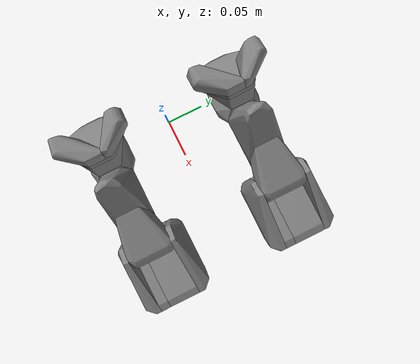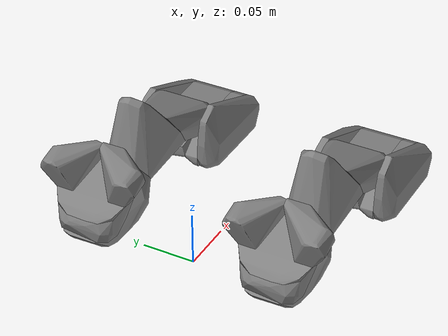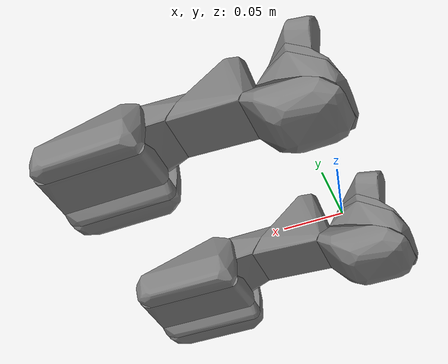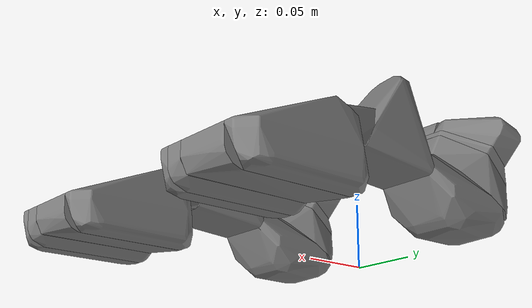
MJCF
<mujoco model="MuJoCo Model">
  <compiler angle="radian"/>

  <option gravity="0 0 -9.81" integrator="implicitfast"/>

  <asset>
    <mesh name="/HyperLegRL/lft/collisions/hull_000_26" vertex="-0.0710905 0.0289914 0.0444284 -0.0729056 0.0289971 0.0534932 -0.0747206 0.0289914 0.0389905 -0.0555321 0.02294 0.0179831 -0.0801594 0.0289971 0.0371794 -0.0729056 0.0289347 0.0571155 -0.035089 0.0150946 0.0179831 -0.0353311 0.0149073 0.0184688 -0.0342166 0.013596 0.0179831 -0.0892218 0.0289914 0.0371794 -0.0874068 0.0289914 0.0607423 -0.0341974 0.0117794 0.0179831 -0.0722241 0.0226618 0.0595803 -0.0928455 0.0287303 0.0589312 -0.0731285 0.0208452 0.0605517 -0.0722241 -0.0226618 0.0595803 -0.0786818 0.0226618 0.0637246 -0.0741283 0.0208452 0.061455 -0.090521 0.0277142 0.0618726 -0.0928455 0.0278277 0.0602612 -0.093839 0.0274417 0.0599207 -0.0837831 0.0226618 0.0643555 -0.0342166 -0.013596 0.0179831 -0.0731285 -0.0208452 0.0605517 -0.0731348 -0.0226618 0.0605471 -0.0739436 0.0219352 0.0179831 -0.0976092 0.0277312 0.0430985 -0.0964756 0.0289914 0.0498664 -0.0786818 -0.0226618 0.0637246 -0.0921004 0.0238766 0.0617818 -0.0959406 0.0226618 0.0584546 -0.0921768 0.0226618 0.0618454 -0.0855981 -0.0226618 0.0642829 -0.0837831 -0.0226618 0.0643555 -0.081968 0.0226618 0.064233 -0.0741283 -0.0226618 0.0614504 -0.0936289 0.0226618 0.0363805 -0.0985263 0.0262836 0.0462396 -0.0980486 0.0280888 0.0498664 -0.0883875 0.0237631 0.0634885 -0.0985326 0.0226618 0.0534932 -0.0967749 0.0208452 0.0571155 -0.0874068 -0.0226618 0.0638471 -0.035089 -0.0150946 0.0179831 -0.0729056 -0.0289347 0.0571155 -0.0961572 0.0226618 0.0392265 -0.0980359 0.0226618 0.0426128 -0.0967749 -0.0208452 0.0571155 -0.0910368 -0.0208452 0.0624854 -0.0783443 -0.0280888 0.0623038 -0.0547806 -0.0228037 0.0179831 -0.0692818 -0.0285032 0.0480507 -0.0747206 -0.0289971 0.0571155 -0.099074 -0.0226618 0.0459173 -0.0992587 0.0226618 0.0480507 -0.0991377 0.0208452 0.0498891 -0.0985326 -0.0226618 0.0534932 -0.0959852 -0.027788 0.0567524 -0.0837831 -0.0287303 0.062558 -0.081968 -0.0289971 0.0607423 -0.0739436 -0.0219352 0.0179831 -0.0921004 -0.0275325 0.036149 -0.0964756 -0.028946 0.0444284 -0.0710905 -0.0229627 0.0179831" face="18 21 34 10 27 13 10 13 18 10 5 1 10 1 27 10 18 34 4 2 3 4 27 1 9 27 4 9 3 25 9 4 3 38 37 54 38 13 27 38 20 13 36 25 60 36 60 61 36 61 45 26 37 38 26 36 45 26 27 9 26 38 27 26 9 25 26 25 36 46 26 45 46 54 37 46 37 26 59 62 52 59 58 62 59 52 44 59 44 58 42 58 32 33 34 21 33 21 32 33 28 34 33 32 58 51 50 43 51 43 44 51 62 61 51 61 50 51 52 62 51 44 52 49 58 44 49 28 33 49 33 58 22 44 43 15 22 11 15 24 44 15 44 22 12 11 8 12 15 11 12 8 5 12 17 14 7 8 6 7 6 5 7 5 8 63 61 60 63 50 61 57 62 58 57 56 62 57 47 56 57 48 47 57 42 48 57 58 42 40 55 56 40 20 38 40 54 55 40 38 54 53 62 56 53 54 46 53 55 54 53 56 55 53 61 62 53 45 61 53 46 45 39 21 18 39 32 21 39 42 32 39 31 48 39 48 42 30 31 20 30 41 47 30 40 41 30 20 40 30 48 31 30 47 48 19 18 13 19 13 20 19 20 18 29 20 31 29 18 20 29 31 39 29 39 18 23 14 17 23 24 15 35 17 28 35 28 49 35 24 23 35 23 17 35 44 24 35 49 44 16 10 34 16 5 10 16 34 28 16 28 17 16 12 5 16 17 12 0 3 2 0 2 4 0 4 1 0 6 3 0 5 6 0 1 5 63 11 22 63 25 3 63 60 25 63 8 11 63 43 50 63 6 8 63 3 6 63 22 43 40 56 47 40 47 41 23 15 12 23 12 14"/>
    <mesh name="/HyperLegRL/lft/collisions/hull_001_27" vertex="-0.0466691 -0.0208451 -0.0386639 -0.0466691 0.0208451 -0.0386639 -0.0462202 -0.0221237 -0.0386639 -0.0466867 -0.0218806 -0.0383257 -0.0740766 -0.0206785 0.0179831 -0.0466163 0.0215474 -0.0386639 -0.0740766 0.0190352 0.0179831 -0.0740678 0.0208451 0.0179831 -0.0458065 -0.0223893 -0.0386639 -0.0739357 0.0219346 0.0179609 -0.0739445 0.0219391 0.0179831 -0.0438966 -0.0229971 -0.0386639 -0.0457097 -0.022709 -0.0371501 -0.0692798 -0.0229971 0.017229 -0.0692798 -0.0229926 0.0154158 -0.0710929 -0.0229386 0.017229 -0.0458065 0.0223893 -0.0386639 -0.072906 0.0225109 0.0179831 -0.0420836 -0.0229971 -0.0335238 -0.071841 0.0228891 0.0179831 -0.0457097 -0.0229971 -0.0190238 -0.0420836 -0.0229746 -0.0317106 -0.038695 -0.0223533 -0.0386639 -0.0438966 0.0229971 -0.0386639 -0.0710929 0.0229611 0.0179831 -0.0547751 -0.0229836 0.0154158 -0.0438966 -0.0229611 -0.0244634 -0.0273853 -0.013511 -0.0386639 0.011464 -0.0109493 -8.23018e-05 0.00323474 -0.0153299 0.00816855 0.00142165 -0.0157126 0.00816855 0.00504782 -0.0149247 0.00635536 -0.0547751 -0.0228035 0.0179831 -0.0700279 0.0229971 0.0179831 0.00323474 -0.0148437 0.00932744 -0.0350777 -0.0150913 0.0179831 -0.0420836 0.0229971 -0.0335238 -0.0565882 0.0229971 0.0179831 0.00472217 -0.0135966 0.00922763 -0.0342063 -0.0135966 0.0179831 -0.0402705 0.0229746 -0.0386639 -0.0547751 0.0229836 0.0154158 0.0152662 -0.00271932 -0.000304099 0.0158383 -0.000904938 0.000915784 0.015011 -0.00541162 0.00454217 -0.0248593 -0.00815795 -0.0386639 -0.0389239 0.0224614 -0.0386639 0.00608638 0.014551 -6.56685e-05 -0.0547751 0.0228981 0.017229 0.0158383 0.000904938 0.000915784 -0.0248593 0.00815795 -0.0386639 0.0154246 0.000904938 -0.000437178 0.0144565 -0.000904938 0.00704848 -0.038695 0.0223533 -0.0386639 0.00323474 0.0153299 0.00816855 0.0158383 0.000904938 0.00454217 -0.0248681 0.00877475 -0.0386639 -0.0249825 0.0105486 -0.0386639 -0.0342063 0.0135966 0.0179831 0.011464 0.0109493 -8.23018e-05 -0.0264787 0.0128897 -0.0386639 0.00323474 0.0135966 0.0095936 -0.0256074 0.0119578 -0.0386639 0.0114376 0.0109178 0.00730354" face="3 0 2 3 4 0 3 15 4 3 2 15 5 1 7 6 7 1 37 54 48 12 11 15 30 21 18 44 43 55 44 55 52 44 52 38 42 51 43 42 43 44 42 44 28 42 45 51 42 27 45 42 28 27 22 27 28 22 18 11 22 30 18 19 24 23 9 7 10 9 5 7 9 10 5 16 10 17 16 5 10 16 17 19 16 19 23 33 23 24 34 38 35 34 30 29 31 22 28 31 34 29 31 38 34 31 28 44 31 44 38 31 29 30 31 30 22 61 37 58 61 54 37 61 38 52 39 35 38 39 38 61 39 61 58 14 15 11 14 11 13 14 13 15 32 4 15 32 15 13 32 13 25 32 34 35 32 25 30 32 30 34 8 11 12 8 15 2 8 12 15 20 21 25 20 18 21 20 25 13 26 25 21 26 30 25 26 21 30 50 51 45 50 56 51 57 51 56 57 62 59 57 59 51 49 43 51 49 55 43 49 51 59 49 59 55 36 40 23 41 37 48 41 48 54 41 54 40 41 36 37 41 40 36 63 55 59 63 54 61 63 52 55 63 61 52 47 40 54 47 54 63 47 63 59 47 46 40 47 53 46 47 59 53 60 59 62 60 53 59 6 1 0 6 0 4 32 35 39 32 33 24 32 6 4 32 10 7 32 17 10 32 7 6 32 24 19 32 58 37 32 19 17 32 37 33 32 39 58 20 11 18 20 13 11 36 33 37 36 23 33 60 16 23 60 23 40 60 11 8 60 2 0 60 22 11 60 45 27 60 0 1 60 46 53 60 1 5 60 50 45 60 62 57 60 27 22 60 5 16 60 8 2 60 56 50 60 57 56 60 40 46"/>
    <mesh name="/HyperLegRL/lft/collisions/hull_002_28" vertex="-0.00123394 0.0135901 -0.0390096 -0.00123394 0.0144337 -0.0392399 -0.00603261 0.0135901 -0.0390096 -0.00123394 -0.0135901 -0.0390096 -0.00123394 0.0151612 -0.0394431 -0.00603261 0.0151612 -0.0394431 -0.00603261 -0.0135901 -0.0390096 -0.00603261 -0.0137681 -0.039057 -0.00123394 -0.0143254 -0.039206 -0.00123394 0.0388356 -0.0647245 -0.00220298 0.0384718 -0.065009 -0.0031288 0.0380849 -0.065246 -0.00603261 0.0351981 -0.0663499 -0.00603261 -0.0151612 -0.0394431 -0.00123394 -0.0151612 -0.0394431 -0.00123394 0.0394779 -0.0659775 -0.00123394 0.0395321 -0.0661535 -0.0031288 0.0380849 -0.0654492 -0.00603261 0.0355619 -0.0681108 -0.0050786 0.0363745 -0.0666344 -0.00603261 -0.0351981 -0.0663499 -0.0031288 -0.0380849 -0.065246 -0.00220298 -0.0384718 -0.065009 -0.00123394 -0.0388356 -0.0647245 -0.0050786 0.0363745 -0.067657 -0.0050786 -0.0363745 -0.0666344 -0.0031288 -0.0380849 -0.0654492 -0.00123394 -0.0395321 -0.0661535 -0.00123394 0.0389981 -0.0689505 -0.00603261 0.0348112 -0.0718898 -0.00603261 -0.0354767 -0.0685577 -0.0050786 -0.0363745 -0.067657 -0.00123394 -0.0391916 -0.0679753 -0.00123394 0.0359101 -0.0842969 -0.0048987 0.0326132 -0.0869652 -0.00123394 0.034966 -0.086139 -0.00603261 0.0319244 -0.0862202 -0.00603261 -0.0323191 -0.0842901 -0.00123394 0.0345016 -0.0869584 -0.00401563 0.0278226 -0.0999479 -0.00603261 0.0280703 -0.100232 -0.0030217 0.0274666 -0.0997786 -0.00603261 0.0172198 -0.106714 -0.00603261 -0.0319244 -0.0862202 -0.0048987 -0.0326132 -0.0869652 -0.00123394 -0.0359101 -0.0842969 -0.00123394 0.0336812 -0.0870262 -0.00293809 0.0117791 -0.100232 -0.00511289 0.0117791 -0.106483 -0.00603261 0.0153315 -0.107492 -0.00603261 0.0166549 -0.106984 -0.00603261 -0.0289758 -0.0987899 -0.00123394 -0.0356857 -0.0848116 -0.00123394 0.0317232 -0.0870532 -0.00361496 0.0117791 -0.10242 -0.00423921 0.0117791 -0.104228 -0.00123394 -0.034966 -0.086139 -0.00123394 -0.0317232 -0.0870532 -0.00603261 0.00452746 -0.10819 -0.00603261 -0.0280703 -0.100232 -0.00401563 -0.0285192 -0.0987899 -0.00123394 -0.0345016 -0.0869584 -0.0030217 -0.0274666 -0.0997786 -0.00603261 -0.0153392 -0.107492" face="1 2 0 23 14 13 8 13 14 5 4 9 5 1 4 5 2 1 7 13 8 3 6 7 3 7 8 22 27 23 22 23 13 11 15 16 33 40 34 21 27 22 21 13 20 21 22 13 52 45 51 60 62 61 36 34 40 36 33 34 12 5 11 17 24 18 17 18 11 17 16 24 17 11 16 10 9 15 10 15 11 10 5 9 10 11 5 28 24 16 25 20 30 25 21 20 26 27 21 56 52 51 56 51 60 56 60 61 44 43 51 44 51 45 44 45 43 37 43 45 37 45 32 31 32 27 31 27 26 31 30 37 31 37 32 31 25 30 59 63 62 59 60 51 59 62 60 48 58 49 48 63 58 48 49 41 48 41 55 48 62 63 48 55 62 57 47 53 57 61 62 57 62 47 54 55 41 54 41 47 54 62 55 54 47 62 29 18 24 29 24 28 29 28 33 29 33 36 19 18 12 19 11 18 19 12 11 39 42 40 39 41 42 39 38 41 50 41 49 50 42 41 46 53 47 46 47 41 46 41 38 35 40 33 35 39 40 35 38 39 3 2 6 3 0 2 31 26 21 31 21 25 50 6 2 50 20 13 50 51 43 50 2 5 50 49 58 50 58 63 50 13 7 50 59 51 50 7 6 50 30 20 50 12 18 50 40 42 50 37 30 50 36 40 50 5 12 50 18 29 50 43 37 50 63 59 50 29 36 35 23 27 35 0 3 35 1 0 35 16 15 35 28 16 35 4 1 35 9 4 35 14 23 35 8 14 35 56 61 35 3 8 35 57 53 35 15 9 35 27 32 35 45 52 35 32 45 35 53 46 35 33 28 35 52 56 35 61 57 35 46 38"/>
    <mesh name="/HyperLegRL/lft/collisions/hull_003_29" vertex="-0.0242141 -0.0289971 -0.102415 -0.0275876 -0.0288211 -0.104227 -0.0242141 -0.0289914 -0.0897289 -0.0257744 -0.0289914 -0.0860966 -0.0493363 -0.0289914 -0.0607249 -0.0257744 -0.0287473 -0.0842843 -0.0493363 -0.0289914 -0.0589126 -0.0511496 -0.0288041 -0.0589126 -0.0457133 -0.0284351 -0.0806598 -0.0420903 -0.0289744 -0.0571004 -0.0386992 -0.0223553 -0.0386639 -0.040277 -0.022974 -0.0386639 -0.0384637 -0.0288211 -0.0625371 -0.0439 -0.0289801 -0.0552881 -0.0242141 -0.013596 -0.0390013 -0.0466691 -0.0208452 -0.0386639 -0.052239 -0.0275439 -0.0578849 -0.0538379 -0.0253526 -0.0777962 -0.0372057 -0.0270216 -0.102752 -0.0466691 0.0208452 -0.0386639 -0.0578791 -0.0117794 -0.064522 -0.0585046 -0.013596 -0.0661695 -0.0582867 -0.0154069 -0.0661695 -0.059239 -0.0154069 -0.069135 -0.0320716 -0.0199086 -0.116003 -0.0591195 0.0117794 -0.0677386 -0.0600894 -0.013596 -0.0752308 -0.0524814 0.0279015 -0.0589126 -0.060114 -0.0117794 -0.0752308 -0.0242141 -0.0206011 -0.116748 -0.0249767 0.0105475 -0.0386639 -0.057612 0.0201356 -0.0684996 -0.059362 -0.0117794 -0.0798988 -0.0539046 -0.0217989 -0.0852571 -0.0392509 -0.0178819 -0.112284 -0.0242141 0.0133405 -0.0389542 -0.0442022 0.0229457 -0.0386639 -0.0475266 0.0289233 -0.0571004 -0.0600859 0.013596 -0.0752308 -0.0573028 -0.0175413 -0.0829271 -0.0257744 -0.0154069 -0.118537 -0.0475266 0.0289971 -0.0589126 -0.0420903 0.0289971 -0.0752308 -0.0515291 0.026891 -0.0770431 -0.0575839 0.0200845 -0.0799616 -0.0293974 -0.0117794 -0.118411 -0.0348372 -0.0117794 -0.116474 -0.0242141 0.0151628 -0.0394406 -0.040277 0.0289914 -0.0607249 -0.040277 0.022974 -0.0386639 -0.0439 0.0287246 -0.0806598 -0.0572676 0.0117794 -0.0847393 -0.0446064 -0.013596 -0.10662 -0.0242141 -0.013596 -0.118702 -0.0408182 0.0117794 -0.11201 -0.0413804 0.0272827 -0.0946009 -0.0537149 0.0234112 -0.0830761 -0.0344963 0.0154069 -0.116293 -0.0242141 0.0117794 -0.118788 -0.0446064 0.013596 -0.10662 -0.0407092 0.0230932 -0.106039 -0.0357298 0.0199256 -0.114191 -0.0401751 0.0207147 -0.10953 -0.0350094 0.020919 -0.113838" face="20 15 19 20 21 15 38 31 44 38 32 28 52 34 39 52 39 32 3 5 9 3 9 13 12 10 9 12 5 10 12 9 5 2 3 0 2 5 3 1 0 4 1 29 0 8 4 7 8 7 17 8 17 18 8 18 1 8 1 4 11 9 10 11 13 9 11 15 7 11 7 13 6 7 4 6 13 7 6 3 13 6 4 0 6 0 3 26 23 28 26 28 32 26 32 39 26 39 17 26 17 23 16 7 15 16 17 7 16 23 17 22 15 21 22 21 23 22 16 15 22 23 16 25 21 20 25 31 38 25 19 31 25 20 19 25 23 21 25 28 23 25 38 28 14 30 10 14 10 5 14 5 2 35 49 30 35 47 49 35 30 14 24 34 46 24 40 29 24 18 34 24 1 18 24 29 1 54 46 34 54 34 52 54 52 59 54 57 46 54 61 57 63 60 55 63 57 61 63 58 57 45 40 24 45 24 46 45 46 57 45 57 58 53 29 40 53 40 45 53 45 58 51 44 59 51 38 44 51 32 38 51 59 52 51 52 32 33 39 34 33 17 39 33 34 18 33 18 17 27 44 31 27 43 44 27 31 19 27 37 41 62 61 54 62 54 59 62 63 61 62 60 63 62 59 44 62 44 60 56 44 43 56 60 44 56 43 55 56 55 60 48 49 47 48 47 58 48 37 49 48 55 42 48 42 41 48 41 37 48 63 55 48 58 63 50 41 42 50 27 41 50 43 27 50 55 43 50 42 55 36 49 37 36 27 19 36 37 27 53 0 29 53 58 47 53 47 35 53 2 0 53 14 2 53 35 14 36 19 15 36 11 10 36 10 30 36 30 49 36 15 11"/>
    <mesh name="/HyperLegRL/lft/collisions/hull_004_30" vertex="-0.00603261 -0.0355696 -0.0681139 -0.00603261 -0.0351935 -0.0663541 -0.00708975 -0.0347131 -0.0667295 -0.0242141 -0.0289055 -0.0879108 -0.0242141 -0.028996 -0.0897254 -0.0242141 -0.028996 -0.10242 -0.0242141 -0.0289264 -0.104227 -0.0242141 -0.0286339 -0.106042 -0.0239578 -0.0286339 -0.106042 -0.0242141 -0.0231397 -0.060738 -0.00603261 -0.0151595 -0.0394394 -0.0242141 -0.0151595 -0.0394394 -0.0242141 -0.0159046 -0.0407848 -0.00603261 -0.0319277 -0.0862213 -0.00603261 -0.0325613 -0.0830848 -0.00603261 -0.0137668 -0.0390561 -0.0242141 -0.0135928 -0.0390014 -0.00603261 -0.0289751 -0.0987909 -0.00603261 -0.0135928 -0.0390092 -0.0242141 -0.0117683 -0.0389466 -0.0192629 -0.0272343 -0.10885 -0.0242141 -0.00815426 -0.0388841 -0.0242141 -0.00996477 -0.0388997 -0.0160239 -0.0252845 -0.110437 -0.00603261 -0.0280699 -0.10023 -0.0242141 0.0135928 -0.0390014 -0.0242141 0.0133351 -0.0389545 -0.0242141 0.0114689 -0.0389154 -0.00603261 0.0151595 -0.0394394 -0.0119145 -0.0220116 -0.110805 -0.0242141 0.0151595 -0.0394394 -0.00603261 0.0351935 -0.0663541 -0.0148938 -0.0232302 -0.112041 -0.0120391 -0.0200897 -0.11251 -0.00603261 -0.0153406 -0.107496 -0.0242141 0.0159046 -0.0407848 -0.00708975 0.0347131 -0.0667295 -0.00603261 0.0355696 -0.0681139 -0.0242141 0.0289055 -0.0876605 -0.0242141 0.0231328 -0.060738 -0.0242141 -0.023843 -0.114473 -0.0242141 0.0286339 -0.106042 -0.0242141 0.0289264 -0.104227 -0.0242141 0.028996 -0.10242 -0.0242141 0.028996 -0.0894673 -0.0239578 0.0286339 -0.106042 -0.00890149 -0.0117822 -0.112002 -0.0119857 -0.0154033 -0.114356 -0.00603261 0.0319277 -0.0862213 -0.00719653 -0.00452628 -0.109937 -0.00603261 -0.00452628 -0.108185 -0.0117615 -0.0117822 -0.11452 -0.00603261 0.0280699 -0.10023 -0.0160239 0.0252845 -0.110437 -0.0172323 0.0255073 -0.110758 -0.0192807 0.0272273 -0.108842 -0.00603261 0.0117822 -0.108091 -0.00889971 0.00452628 -0.112025 -0.00603261 0.0172207 -0.106714 -0.00659855 0.0117822 -0.108959 -0.0221443 0.0154033 -0.118416 -0.0137067 0.0190312 -0.11438 -0.00603261 0.0149158 -0.107614 -0.0242141 0.023843 -0.114473" face="2 9 3 2 3 0 22 18 21 11 10 16 15 18 16 15 16 10 1 2 0 1 10 11 1 11 12 1 12 9 1 9 2 36 38 39 36 37 38 19 16 18 19 18 22 4 0 3 4 5 0 6 7 0 6 0 5 8 0 7 8 7 20 23 32 24 49 46 57 49 57 59 49 59 50 51 57 46 51 46 47 51 47 60 34 49 50 34 46 49 34 24 33 34 47 46 34 33 47 61 58 62 61 62 59 61 52 58 61 53 52 61 59 57 61 57 51 61 51 60 40 20 7 40 32 23 40 23 20 40 60 47 40 33 32 40 47 33 29 24 32 29 32 33 29 33 24 31 37 36 31 30 28 31 35 30 31 39 35 31 36 39 25 28 30 25 26 28 27 18 28 27 28 26 27 21 18 44 38 37 44 37 43 42 37 41 42 43 37 45 37 48 45 41 37 45 48 52 45 52 55 45 55 41 54 52 53 54 55 52 54 53 61 63 41 55 63 60 40 63 55 54 63 61 60 63 54 61 56 50 59 56 59 62 14 0 8 14 8 13 17 13 8 17 8 20 17 23 24 17 20 23 63 16 19 63 25 30 63 3 9 63 9 12 63 12 11 63 22 21 63 39 38 63 40 7 63 7 6 63 21 27 63 11 16 63 4 3 63 30 35 63 38 44 63 19 22 63 5 4 63 6 5 63 42 41 63 35 39 63 26 25 63 27 26 63 44 43 63 43 42 17 37 31 17 1 0 17 50 56 17 34 50 17 18 15 17 58 52 17 28 18 17 15 10 17 48 37 17 0 14 17 10 1 17 52 48 17 62 58 17 24 34 17 31 28 17 56 62 17 14 13"/>
    <mesh name="/HyperLegRL/lft/collisions/hull_005_31" vertex="0.00867602 0.0135999 -0.0390029 0.0102017 0.0135999 -0.0394403 0.00999735 0.0149455 -0.0395861 0.00867602 0.015168 -0.0394403 -0.00123394 0.0135999 -0.0390029 0.00867602 -0.00683358 -0.0390029 0.00979299 -0.00683358 -0.0393227 0.0225108 0.0371643 -0.059342 0.0224268 0.038547 -0.0595066 0.0211335 0.040788 -0.0591962 0.0208059 0.0421442 -0.0594361 0.0190843 0.0439772 -0.0595396 0.0171527 0.0454394 -0.059723 -0.00123394 0.015168 -0.0394403 -0.00123394 0.00997622 -0.0390029 0.00637489 -0.00683358 -0.0390029 0.01091 -0.00683358 -0.0407809 0.0224576 0.0353525 -0.0594361 0.0229923 0.0371643 -0.0607249 0.0221804 0.0414502 -0.0619338 0.0147396 0.047087 -0.0620702 0.0164024 0.0454394 -0.059723 0.00591579 0.0453494 -0.0633967 0.00396739 0.0436647 -0.0633073 0.00226814 0.0417575 -0.0634061 -0.00123394 0.0388331 -0.0647231 -0.00123394 0.00912858 -0.0390264 -0.00123394 -0.00683358 -0.039525 0.0109995 -0.00683358 -0.0425966 0.024126 0.0359088 -0.0650947 0.0259793 0.0383192 -0.0721974 0.0273622 0.0371643 -0.0770376 0.0186952 0.04536 -0.0614446 0.0123013 0.0472566 -0.0625406 0.0100533 0.0469175 -0.0625406 -0.00123394 0.0395271 -0.0661484 6.05653e-07 0.0402688 -0.0648172 -0.00123394 -0.00683358 -0.0480012 0.0109995 -0.00683358 -0.0444075 0.0263292 0.0319248 -0.0770376 0.0100505 0.0470499 -0.0643468 0.0124664 0.0467374 -0.07692 0.0048968 0.0441362 -0.0662378 0.00867602 -0.00683358 -0.0480012 -0.00123394 0.017605 -0.0865299 0.0109352 -0.00683358 -0.045734 0.01091 -0.00683358 -0.0462232 0.0263152 0.040788 -0.0788486 0.0264552 0.040788 -0.0770376 0.0259373 0.0371643 -0.0797705 0.0259037 0.0417098 -0.0797611 0.0253802 0.0427852 -0.0788486 0.0149355 0.0471665 -0.0816238 -0.00123394 0.0359141 -0.0843003 -0.00122274 0.0180818 -0.0870285 0.0251674 0.0299117 -0.0788486 0.023177 0.0299117 -0.0804949 0.0223624 0.0271251 -0.0798505 0.00218695 0.0381762 -0.0853069 -0.00123394 0.0349711 -0.0861394 0.0159265 0.044417 -0.0824564 -0.00123394 0.0344095 -0.0870002 0.00901195 0.0439296 -0.0824752 -0.00123394 0.0208472 -0.0870567" face="23 22 35 23 13 22 3 0 2 9 10 2 9 8 10 9 2 8 1 8 2 1 2 0 16 39 31 16 28 39 38 39 28 43 37 44 43 57 46 43 44 57 47 31 50 47 48 31 47 50 48 30 31 48 30 18 31 30 8 18 19 10 8 19 32 10 19 8 30 19 30 48 49 56 63 49 50 31 54 44 63 54 63 56 54 57 44 54 56 57 55 57 56 55 46 57 55 39 46 55 56 49 55 31 39 55 49 31 41 22 40 41 40 52 41 62 22 41 52 62 34 40 22 34 22 13 34 13 21 33 20 52 33 52 40 33 40 34 33 21 20 33 34 21 11 2 10 11 10 32 51 48 50 51 50 52 51 19 48 51 32 19 51 52 20 51 20 32 12 20 21 12 32 20 12 11 32 12 2 11 12 3 2 60 63 61 60 49 63 60 50 49 60 52 50 60 61 52 42 35 22 42 22 62 42 53 35 42 62 53 58 61 59 58 59 53 58 53 62 58 52 61 58 62 52 29 31 18 29 18 17 29 16 31 29 17 16 7 17 18 7 18 8 7 8 1 7 16 17 7 1 16 36 35 25 36 23 35 36 25 23 24 25 13 24 13 23 24 23 25 26 27 15 26 15 14 6 16 1 6 0 5 6 1 0 45 46 39 45 39 38 3 13 4 3 4 0 14 15 5 14 0 4 14 5 0 12 13 3 12 21 13 26 63 44 26 4 13 26 25 35 26 61 63 26 37 27 26 14 4 26 44 37 26 59 61 26 13 25 26 35 53 26 53 59 45 27 37 45 5 15 45 6 5 45 15 27 45 37 43 45 28 16 45 38 28 45 43 46 45 16 6"/>
    <mesh name="/HyperLegRL/lft/collisions/hull_006_32" vertex="0.0141125 -0.0472883 -0.0661578 0.0123013 -0.0472606 -0.0625406 0.0123013 -0.0472606 -0.0643468 0.0188827 -0.0472131 -0.0788486 0.0123013 -0.0471933 -0.0615293 0.0112263 -0.0471616 -0.0615951 0.0109603 -0.0471814 -0.0625406 0.0123013 -0.0472408 -0.0679734 0.0188379 -0.0471893 -0.0800386 0.0197897 -0.0468884 -0.0788486 0.0150615 -0.0471537 -0.0632744 0.0171527 -0.0454391 -0.059723 0.00591579 -0.045348 -0.0633967 -0.00123394 -0.0151653 -0.0394403 0.0149355 -0.0471656 -0.0816238 0.0159265 -0.0471696 -0.0816238 0.00867602 -0.0151653 -0.0394403 0.0183592 -0.0451856 -0.0602357 0.00396739 -0.043665 -0.0633073 -0.00123394 -0.0395308 -0.0661484 -0.00123394 -0.0388378 -0.0647231 0.00226814 -0.0417603 -0.0634061 0.0176286 -0.0462073 -0.0817414 0.0202936 -0.0433561 -0.0603533 0.0102017 -0.0136011 -0.0394403 0.00867602 -0.0136011 -0.0390029 0.0224268 -0.0385448 -0.0595066 6.05653e-07 -0.0402713 -0.0648172 0.00901195 -0.0439303 -0.0824752 0.0159265 -0.0444174 -0.0824564 0.0260268 -0.041883 -0.0788486 0.024364 -0.0438076 -0.0770376 0.0223876 -0.0454113 -0.0756171 0.0229699 -0.044255 -0.073411 0.0220321 -0.0408257 -0.0606403 -0.00123394 -0.0345334 -0.0869297 0.027057 -0.0389764 -0.0770376 0.0259037 -0.0417048 -0.076111 0.0224576 -0.0353491 -0.0594361 0.01091 -0.00683358 -0.0407809 0.0259793 -0.0383191 -0.0721974 0.0273622 -0.0371628 -0.0770376 0.024126 -0.0359075 -0.0650947 -0.00123394 -0.00683358 -0.039525 0.0259373 -0.0371628 -0.0797705 0.01049 -0.0244751 -0.0839146 -0.00123394 -0.0280034 -0.0870567 0.0109995 -0.00683358 -0.0425966 0.0222336 -0.032787 -0.0599488 0.0269563 -0.0335394 -0.0770376 0.0263292 -0.0319238 -0.0770376 -0.00123394 -0.00683358 -0.0480012 0.02428 -0.0288192 -0.0799022 0.0265811 -0.0335394 -0.0788486 -0.00123394 -0.0173433 -0.0861065 0.00867602 -0.00683358 -0.0480012 0.0223624 -0.0271283 -0.0798505 0.01091 -0.00683358 -0.0462232 0.0173262 -0.0251245 -0.081779 -0.00122274 -0.0180798 -0.0870285 -0.00123394 -0.0180759 -0.0870285 0.000952409 -0.017961 -0.0855044 0.00908753 -0.00683358 -0.0478836 0.00446009 -0.0197707 -0.0853304" face="57 52 56 57 54 62 55 54 51 55 62 54 12 13 18 12 18 19 11 16 13 11 24 16 11 17 24 34 40 26 34 37 40 23 33 31 23 31 37 23 37 34 23 34 26 23 26 24 23 24 17 32 31 33 32 9 31 32 33 23 32 23 17 42 40 41 42 26 40 38 48 39 38 24 26 38 39 24 38 26 42 38 42 48 25 13 16 25 16 24 25 43 13 25 39 43 25 24 39 58 56 52 58 59 63 58 57 56 53 52 50 53 41 44 53 44 52 49 39 48 49 50 39 49 42 41 49 48 42 49 41 53 49 53 50 47 39 50 47 50 52 47 52 57 61 54 57 61 63 59 61 59 54 61 58 63 61 57 58 30 44 41 30 37 31 30 22 44 30 31 9 29 35 46 29 44 22 29 15 35 29 22 15 60 59 46 60 54 59 45 46 59 45 29 46 45 44 29 45 52 44 45 58 52 45 59 58 21 13 20 21 18 13 21 20 18 27 20 19 27 19 18 27 18 20 5 12 6 5 1 4 5 6 1 5 13 12 5 11 13 5 4 11 14 35 15 14 0 7 14 6 12 14 7 6 14 3 0 14 15 3 28 19 35 28 12 19 28 35 14 28 14 12 2 7 0 2 0 1 2 6 7 2 1 6 36 41 40 36 40 37 36 30 41 36 37 30 8 3 15 8 9 3 8 15 22 8 30 9 8 22 30 10 3 9 10 9 32 10 32 17 10 0 3 10 1 0 10 4 1 10 11 4 10 17 11 47 51 43 47 57 62 47 43 39 47 62 55 47 55 51 60 20 13 60 13 43 60 46 35 60 35 19 60 51 54 60 43 51 60 19 20"/>
    <mesh name="/HyperLegRL/lto/collisions/hull_000_33" vertex="0.0124935 0.0435442 0.0335 0.0104945 0.0435035 0.0384989 0.013493 0.0434687 0.0325017 0.013493 0.0434687 0.0272394 -0.0674978 0.0435442 0.0272394 -0.0674978 0.0435384 0.0384989 -0.0684973 0.0435151 0.0315016 -0.0684973 0.043521 0.0335 -0.0694969 0.043428 0.0345002 0.00549686 0.0429692 0.0423811 -0.0624903 0.0432654 0.0414993 0.0151556 0.0428646 0.0355003 0.0172041 0.0410757 0.0355003 -0.0727923 0.0427194 0.0315016 0.00549686 0.0412674 0.0443939 -0.0614908 0.0417727 0.0439871 -0.0740788 0.0408608 0.0400869 0.0185401 0.037283 0.0325017 -0.0614908 0.039281 0.0453367 -0.0650139 0.0397921 0.0450033 -0.0762362 0.0409479 0.0325017 0.0176791 0.037283 0.0374988 0.00549686 0.037283 0.04555 0.00849542 0.037283 0.0452507 -0.0723866 0.0242843 0.045274 -0.0728814 0.0242843 0.0448886 0.0132258 0.0332811 0.0431608 0.0147795 0.0342801 0.0417825 0.00979183 0.0342801 0.0449424 -0.0614908 0.037283 0.04555 -0.0723866 0.0192834 0.045274 -0.0714959 0.0242843 0.04555 -0.0788686 0.0386305 0.0325017 0.018263 0.0182844 0.0353784 0.0074959 0.0182844 0.0454819 -0.0714959 0.0192834 0.04555 -0.081887 0.0192834 0.0358892 -0.0778889 0.0242843 0.039888 -0.0825401 0.0242843 0.0345002 -0.0800166 0.0368183 0.0330968 -0.0733861 0.0192834 0.0443886 0.0142253 -0.00650489 0.0351848 0.0150764 -0.00371115 0.0351114 0.0182135 0.0172796 0.0277574 -0.0714959 0.0182844 0.0454819 -0.0825401 0.0192834 0.0345002 -0.0722084 0.0176688 0.0451378 -0.0805411 0.036284 0.0272394 0.013493 -0.00570917 0.0274509 -0.0824807 0.0182844 0.0345002 -0.0823125 0.0312831 0.0272394 0.00814905 -0.0102976 0.035106 0.0153139 -0.00271215 0.0285012 0.0182729 0.0323634 0.0272394 -0.0814911 0.0171925 0.0345002 -0.080165 0.0167104 0.0350988 -0.00346913 -0.015403 0.0345002 0.0139186 -0.0071554 0.0285012 -0.0025092 -0.0157864 0.0335 -0.0822036 0.0175932 0.0272394 -0.0744945 0.0142652 0.0335 -0.00346913 -0.015403 0.0285012 -0.00350872 -0.0137128 0.0274509 -0.0025092 -0.0154843 0.0277556" face="56 58 51 56 44 46 56 46 55 57 41 51 57 52 41 57 48 52 57 63 48 57 51 58 57 58 63 61 63 58 61 59 63 61 60 59 61 58 56 61 56 60 62 63 59 62 48 63 62 59 53 62 53 48 0 1 2 6 8 7 6 7 4 3 4 0 3 0 2 3 17 53 3 12 17 43 52 48 43 48 53 43 33 52 43 53 17 43 17 33 13 8 6 13 6 4 13 4 47 13 47 20 16 24 19 16 39 38 16 38 37 16 13 20 50 38 39 50 39 47 32 47 39 32 20 47 32 39 16 32 16 20 54 59 60 54 49 59 54 56 55 54 60 56 54 55 46 54 46 49 45 59 49 45 50 59 45 38 50 36 46 40 36 49 46 36 40 37 36 45 49 36 37 38 36 38 45 18 29 22 18 19 29 18 22 14 5 7 8 5 16 10 5 10 1 5 8 13 5 13 16 5 1 0 5 4 7 5 0 4 9 14 1 9 1 10 15 19 18 15 18 14 15 16 19 15 10 16 15 14 9 15 9 10 30 46 44 30 40 46 35 30 44 31 29 19 31 19 24 25 37 40 25 30 24 25 40 30 25 16 37 25 24 16 42 33 27 42 41 52 42 52 33 26 42 27 34 51 41 34 26 28 34 41 42 34 42 26 34 44 56 34 56 51 34 22 35 34 35 44 23 14 22 23 22 34 23 34 28 23 12 14 23 26 27 23 28 26 11 2 1 11 1 14 11 14 12 11 3 2 11 12 3 21 33 17 21 17 12 21 27 33 21 23 27 21 12 23 50 4 3 50 53 59 50 47 4 50 3 53 31 35 22 31 22 29 31 24 30 31 30 35"/>
    <mesh name="/HyperLegRL/lto/collisions/hull_001_34" vertex="0.0124935 0.0435442 -0.0335003 0.013493 0.0434687 -0.0272452 0.013493 0.0434687 -0.0325005 0.011494 0.0435035 -0.0374995 -0.0634997 0.0435442 -0.0394992 -0.0684973 0.0435151 -0.029501 -0.0684973 0.0435093 -0.0272452 -0.0694969 0.0434455 -0.0325005 0.00549686 0.0429692 -0.0423821 -0.0614908 0.0429692 -0.0423821 -0.0704964 0.0433119 -0.0364997 0.0151556 0.0428646 -0.0355017 -0.0614908 0.0417727 -0.0439876 -0.0721985 0.0428646 -0.0305008 0.0172041 0.0410757 -0.0355017 -0.0730694 0.040855 -0.041067 -0.0741184 0.0418598 -0.0382055 0.0074959 0.0403729 -0.0447975 -0.0614908 0.039281 -0.0453368 -0.0650139 0.0397921 -0.0450035 -0.0762263 0.0409305 -0.0335003 0.0185401 0.037283 -0.0325005 -0.0704964 0.039281 -0.0434536 -0.0723866 0.0242843 -0.0452741 -0.0728814 0.0242843 -0.0448888 0.00849542 0.037283 -0.0452562 0.00549686 0.037283 -0.04555 -0.0614908 0.037283 -0.04555 -0.0723866 0.0192834 -0.0452741 -0.0714959 0.0242843 -0.04555 -0.0778889 0.0242843 -0.039888 -0.081887 0.0242843 -0.0358905 -0.0794228 0.037283 -0.0345001 0.0132258 0.0332811 -0.0431616 0.00980172 0.0342801 -0.0449426 0.018263 0.0182844 -0.0353781 -0.0714959 0.0192834 -0.04555 -0.0733861 0.0192834 -0.0443871 -0.081887 0.0192834 -0.0358905 -0.0800463 0.0359761 -0.0341686 0.0147795 0.0342801 -0.0417819 0.0074959 0.0182844 -0.0454819 -0.0714959 0.0182844 -0.0454819 -0.0722084 0.0176688 -0.0451379 -0.0825401 0.0242843 -0.0345001 0.0182135 0.0172796 -0.0277576 0.0150764 -0.00371115 -0.0351111 0.0142253 -0.00650489 -0.0351846 -0.0824807 0.0182844 -0.0345001 0.0182729 0.0323634 -0.0272452 0.013493 -0.00570917 -0.0274512 -0.00346913 -0.015403 -0.0345001 -0.0814911 0.0171925 -0.0345001 -0.080165 0.0167104 -0.0350985 -0.0825401 0.0192834 -0.0272452 0.0153139 -0.00271215 -0.0285012 0.00814905 -0.0102976 -0.0351057 -0.0025092 -0.0157864 -0.0335003 -0.00346913 -0.015403 -0.0285012 -0.0744945 0.0142652 -0.0335003 -0.0822036 0.0175932 -0.0272452 0.0139186 -0.0071554 -0.0285012 -0.00350872 -0.0137128 -0.0274512 -0.0025092 -0.0154843 -0.0277558" face="20 32 39 14 21 35 14 35 40 14 40 17 51 56 57 51 43 42 51 53 43 61 56 47 61 47 55 61 55 50 61 50 63 61 57 56 61 63 57 58 57 63 58 63 60 58 60 59 58 51 57 58 59 51 62 60 63 62 63 50 62 49 60 62 50 49 54 6 39 54 39 44 54 44 48 54 48 60 0 2 3 7 6 5 1 0 6 1 2 0 1 49 21 1 21 14 45 50 55 45 49 50 45 55 35 45 21 49 45 35 21 13 7 10 13 6 7 13 39 6 13 20 39 52 59 60 52 60 48 52 53 51 52 51 59 52 43 53 52 48 43 31 15 30 31 44 39 31 39 32 31 32 15 38 37 43 38 43 48 38 30 37 38 31 30 38 48 44 38 44 31 18 26 27 18 27 19 18 17 26 4 9 10 4 10 7 4 7 5 4 0 3 4 5 6 4 6 0 8 3 17 8 4 3 8 9 4 12 18 19 12 17 18 12 19 15 12 15 9 12 8 17 12 9 8 28 42 43 28 43 37 36 42 28 29 19 27 24 37 30 24 23 28 24 28 37 24 30 15 16 13 10 16 20 13 16 10 9 16 9 15 16 32 20 16 15 32 22 15 19 22 29 23 22 19 29 22 23 24 22 24 15 46 40 35 46 55 47 46 35 55 33 40 46 41 47 56 41 34 33 41 46 47 41 33 46 41 51 42 41 56 51 41 36 26 41 42 36 25 26 17 25 41 26 25 34 41 25 33 34 25 17 40 25 40 33 11 3 2 11 17 3 11 14 17 11 2 1 11 1 14 1 54 60 1 60 49 1 6 54 29 26 36 29 27 26 29 28 23 29 36 28"/>
    <mesh name="/HyperLegRL/lto/collisions/hull_002_35" vertex="-0.0825401 0.0192902 -0.0272452 -0.0825401 0.0192902 0.0141617 -0.0825401 0.0282892 -0.0244971 -0.0824708 0.0182755 -0.0135172 -0.0825401 0.0282833 0.0141617 -0.0821938 0.0175972 0.0141617 -0.0823323 0.0312829 -0.0264994 -0.0822928 0.0312829 -0.0272452 -0.0821938 0.0175972 -0.0272452 -0.082461 0.030283 -0.00650119 -0.0820157 0.0328403 -0.0135172 -0.0811252 0.0170456 -8.05706e-06 -0.0724875 0.0134531 -0.0272452 -0.0724875 0.013459 0.0141617 -0.0715277 0.0134177 -0.0272452 -0.00251497 0.0159366 -0.0272452 -0.00251497 0.0164557 0.0141617 -0.0809174 0.0356423 -0.0272452 -0.00152554 0.0163053 -0.0272452 0.0182631 0.0323625 -0.0272452 0.0180949 0.0247026 -0.0124958 0.0181938 0.0246229 0.0114948 0.0184708 0.0252866 -0.0114987 0.0183719 0.0332827 0.0141617 0.0185401 0.0342826 -0.0272452 0.0185401 0.0262835 -0.0114987 0.0185401 0.0262835 0.0114948 0.0185401 0.030283 0.0114948 0.0183026 0.039282 -0.0244971 0.0181246 0.0342295 0.0141617 0.0185401 0.0372823 -0.0244971 0.0183224 0.039282 -0.0254983 0.0184807 0.0382822 -0.0272452 0.0183224 0.039282 -0.0272452 0.0178673 0.0405238 -0.0244971 0.0178772 0.0405592 -0.0254983 -0.0767223 0.0405887 -0.0224949 0.0178772 0.0405621 -0.0272452 0.0173825 0.0412671 -0.0254983 0.016957 0.0417478 -0.0244971 -0.07787 0.0377542 0.0141617 -0.0761979 0.0409397 -0.0272452 0.0173825 0.04127 -0.0272452 0.0169768 0.0417685 -0.0272452 0.015839 0.0426976 -0.0244971 0.0158686 0.0427153 -0.0272452 0.0144834 0.0431194 -0.023496 -0.0704888 0.0432197 -0.023496 -0.0694895 0.0434114 -0.0244971 -0.0704888 0.0433052 -0.0272452 0.0144834 0.0432727 -0.0272452 0.0134841 0.0434704 -0.0254983 0.0134841 0.0434409 -0.0244971 -0.0684902 0.0435087 -0.0272452 0.0134841 0.0434704 -0.0272452 0.0124848 0.043547 -0.0254983 0.0134841 0.0381229 0.0141617 -0.0674909 0.043435 -0.023496 -0.0674909 0.0435294 -0.0244971 -0.0674909 0.043547 -0.0272452 0.0114855 0.04355 -0.0254983 -0.0664916 0.04355 -0.0254983 -0.0664916 0.04355 -0.0272452 0.0114855 0.04355 -0.0272452" face="61 58 60 57 60 58 57 52 60 23 32 31 50 52 46 44 45 50 44 50 46 33 37 31 33 31 32 30 24 32 30 23 27 30 32 23 35 37 38 35 38 34 35 31 37 28 34 29 28 29 23 28 23 31 28 31 35 28 35 34 55 60 52 55 54 63 55 63 60 56 46 52 56 29 44 56 44 46 56 52 57 7 6 17 2 9 6 2 4 9 2 7 0 2 6 7 10 17 6 10 6 9 10 9 4 48 53 49 48 49 47 48 58 53 48 57 58 48 47 57 59 61 62 59 53 58 59 58 61 41 17 36 41 47 49 41 36 47 40 47 36 40 10 4 40 57 47 40 56 57 40 36 17 40 17 10 11 8 12 11 5 8 11 13 5 11 12 13 3 5 1 3 0 8 3 1 0 3 8 5 14 15 13 14 13 12 16 13 15 16 21 23 18 19 20 18 20 21 18 16 15 18 21 16 26 23 21 26 27 23 22 21 20 22 25 26 22 26 21 22 20 19 22 19 24 22 24 25 42 38 37 42 43 38 51 50 54 51 52 50 51 54 55 51 55 52 39 44 29 39 29 34 39 34 38 39 38 43 39 43 45 39 45 44 61 63 62 61 60 63 2 1 4 2 0 1 16 4 1 16 1 5 16 23 29 16 5 13 16 40 4 16 29 56 16 56 40 26 24 30 26 25 24 26 30 27 42 37 33 42 63 54 42 8 0 42 18 15 42 59 62 42 41 49 42 32 24 42 49 53 42 24 19 42 54 50 42 0 7 42 62 63 42 12 8 42 15 14 42 45 43 42 50 45 42 33 32 42 7 17 42 53 59 42 17 41 42 14 12 42 19 18"/>
    <mesh name="/HyperLegRL/lto/collisions/hull_003_36" vertex="0.0127508 0.0435293 0.0272394 -0.0105054 0.0435323 0.0244999 -0.0354934 0.0434378 0.0234989 -0.0374924 0.0431752 0.0224991 -0.0684973 0.0434969 0.0272394 -0.040491 0.0428889 0.021813 0.0140076 0.0427885 0.0219922 0.0124935 0.042576 0.0213534 -0.0694969 0.0428535 0.0218629 0.015878 0.0427177 0.0272394 0.0138592 0.0380515 0.0141617 0.0143639 0.0379305 0.0141617 0.016066 0.0418411 0.0219141 0.0167093 0.0414692 0.0224991 -0.0764935 0.0380721 0.0141617 0.017026 0.0408199 0.0219512 0.016927 0.0362924 0.0141617 0.0176593 0.0402031 0.0225708 0.017887 0.0405631 0.0272394 0.0180156 0.0398164 0.022951 0.0182531 0.0392822 0.0234989 0.0184411 0.0382846 0.0234989 0.0183917 0.0332849 0.0141617 0.0185302 0.0375438 0.0272394 0.0185401 0.0372841 0.0244999 0.0184115 0.0332849 0.014501 0.0182531 0.0323759 0.0141617 0.0185401 0.0342825 0.0195011 0.0185104 0.0342825 0.0185 0.0184807 0.0332849 0.0185 0.0182729 0.032367 0.0272394 -0.00151958 0.0163053 0.0272394 -0.00179667 0.0166181 0.0141617 -0.0778592 0.0396659 0.0272394 -0.00239044 0.0159541 0.0272394 -0.00203418 0.0165621 0.0141617 -0.0025092 0.0164529 0.0141617 -0.0717334 0.0134011 0.0272394 -0.0724954 0.0134601 0.0141617 -0.0801353 0.0369653 0.0254997 -0.0801254 0.0369506 0.0272394 -0.0724954 0.0134512 0.0272394 -0.072723 0.0135457 0.0141617 -0.0809171 0.0356077 0.0272394 -0.0726736 0.0135191 0.0272394 -0.0731684 0.0137169 0.0141617 -0.081976 0.0329868 0.0272394 -0.0814911 0.0171966 0.0141617 -0.0823323 0.0312838 0.0254997 -0.0814911 0.0171966 0.0272394 -0.0817385 0.0173324 0.0141617 -0.0822036 0.0175951 0.0272394 -0.0822036 0.0175951 0.0141617 -0.0823125 0.0312838 0.0272394 -0.0824412 0.0302833 0.0254997 -0.0824115 0.0181057 0.0272394 -0.0825104 0.0292828 0.0244999 -0.0823917 0.0300236 0.0272394 -0.0825203 0.0292828 0.0141617 -0.0824807 0.0182857 0.0272394 -0.0825401 0.0282852 0.0244999 -0.0825401 0.024286 0.0272394 -0.0825401 0.0192862 0.0272394 -0.0825401 0.0192862 0.0141617" face="38 34 37 27 28 24 27 30 29 36 34 38 31 34 32 6 11 10 35 32 34 35 34 36 25 27 29 25 28 27 43 39 58 54 53 48 54 48 58 14 5 10 14 39 33 14 58 39 63 60 58 63 59 62 63 52 59 1 4 0 1 2 4 1 0 6 1 6 2 3 2 6 23 27 24 23 30 27 23 20 18 9 18 13 9 6 0 26 30 31 26 31 32 26 22 25 26 29 30 26 25 29 12 11 6 12 16 11 12 9 13 12 6 9 7 10 5 7 6 10 7 5 3 7 3 6 21 25 22 21 22 20 21 24 28 21 28 25 21 23 24 21 20 23 19 20 22 19 22 16 19 16 17 19 18 20 19 17 13 19 13 18 15 13 17 15 17 16 15 12 13 15 16 12 55 52 51 55 59 52 50 49 51 50 51 52 50 47 49 41 38 37 42 41 44 42 38 41 45 44 49 45 49 47 45 42 44 40 33 39 40 39 43 46 48 53 46 58 48 46 43 58 57 53 54 57 60 61 56 58 60 56 54 58 56 60 57 56 57 54 8 5 14 8 3 5 8 33 4 8 14 33 8 4 2 8 2 3 63 62 61 63 61 60 45 11 16 45 32 35 45 10 11 45 36 38 45 50 52 45 52 63 45 14 10 45 35 36 45 16 22 45 26 32 45 58 14 45 63 58 45 22 26 45 47 50 45 38 42 57 34 31 57 37 34 57 9 0 57 0 4 57 30 23 57 4 33 57 46 53 57 51 49 57 55 51 57 33 40 57 31 30 57 61 62 57 62 59 57 49 44 57 41 37 57 23 18 57 18 9 57 59 55 57 44 41 57 40 43 57 43 46"/>
    <mesh name="/HyperLegRL/rft/collisions/hull_000_37" vertex="-0.0710905 0.0289914 0.0444284 -0.0729056 0.0289971 0.0534932 -0.0747206 0.0289914 0.0389905 -0.0555321 0.02294 0.0179831 -0.0801594 0.0289971 0.0371794 -0.0729056 0.0289347 0.0571155 -0.035089 0.0150946 0.0179831 -0.0353311 0.0149073 0.0184688 -0.0342166 0.013596 0.0179831 -0.0892218 0.0289914 0.0371794 -0.0874068 0.0289914 0.0607423 -0.0341974 0.0117794 0.0179831 -0.0722241 0.0226618 0.0595803 -0.0928455 0.0287303 0.0589312 -0.0731285 0.0208452 0.0605517 -0.0722241 -0.0226618 0.0595803 -0.0786818 0.0226618 0.0637246 -0.0741283 0.0208452 0.061455 -0.090521 0.0277142 0.0618726 -0.0928455 0.0278277 0.0602612 -0.093839 0.0274417 0.0599207 -0.0837831 0.0226618 0.0643555 -0.0342166 -0.013596 0.0179831 -0.0731285 -0.0208452 0.0605517 -0.0731348 -0.0226618 0.0605471 -0.0739436 0.0219352 0.0179831 -0.0976092 0.0277312 0.0430985 -0.0964756 0.0289914 0.0498664 -0.0786818 -0.0226618 0.0637246 -0.0921004 0.0238766 0.0617818 -0.0959406 0.0226618 0.0584546 -0.0921768 0.0226618 0.0618454 -0.0855981 -0.0226618 0.0642829 -0.0837831 -0.0226618 0.0643555 -0.081968 0.0226618 0.064233 -0.0741283 -0.0226618 0.0614504 -0.0936289 0.0226618 0.0363805 -0.0985263 0.0262836 0.0462396 -0.0980486 0.0280888 0.0498664 -0.0883875 0.0237631 0.0634885 -0.0985326 0.0226618 0.0534932 -0.0967749 0.0208452 0.0571155 -0.0874068 -0.0226618 0.0638471 -0.035089 -0.0150946 0.0179831 -0.0729056 -0.0289347 0.0571155 -0.0961572 0.0226618 0.0392265 -0.0980359 0.0226618 0.0426128 -0.0967749 -0.0208452 0.0571155 -0.0910368 -0.0208452 0.0624854 -0.0783443 -0.0280888 0.0623038 -0.0547806 -0.0228037 0.0179831 -0.0692818 -0.0285032 0.0480507 -0.0747206 -0.0289971 0.0571155 -0.099074 -0.0226618 0.0459173 -0.0992587 0.0226618 0.0480507 -0.0991377 0.0208452 0.0498891 -0.0985326 -0.0226618 0.0534932 -0.0959852 -0.027788 0.0567524 -0.0837831 -0.0287303 0.062558 -0.081968 -0.0289971 0.0607423 -0.0739436 -0.0219352 0.0179831 -0.0921004 -0.0275325 0.036149 -0.0964756 -0.028946 0.0444284 -0.0710905 -0.0229627 0.0179831" face="18 21 34 10 27 13 10 13 18 10 5 1 10 1 27 10 18 34 4 2 3 4 27 1 9 27 4 9 3 25 9 4 3 38 37 54 38 13 27 38 20 13 36 25 60 36 60 61 36 61 45 26 37 38 26 36 45 26 27 9 26 38 27 26 9 25 26 25 36 46 26 45 46 54 37 46 37 26 59 62 52 59 58 62 59 52 44 59 44 58 42 58 32 33 34 21 33 21 32 33 28 34 33 32 58 51 50 43 51 43 44 51 62 61 51 61 50 51 52 62 51 44 52 49 58 44 49 28 33 49 33 58 22 44 43 15 22 11 15 24 44 15 44 22 12 11 8 12 15 11 12 8 5 12 17 14 7 8 6 7 6 5 7 5 8 63 61 60 63 50 61 57 62 58 57 56 62 57 47 56 57 48 47 57 42 48 57 58 42 40 55 56 40 20 38 40 54 55 40 38 54 53 62 56 53 54 46 53 55 54 53 56 55 53 61 62 53 45 61 53 46 45 39 21 18 39 32 21 39 42 32 39 31 48 39 48 42 30 31 20 30 41 47 30 40 41 30 20 40 30 48 31 30 47 48 19 18 13 19 13 20 19 20 18 29 20 31 29 18 20 29 31 39 29 39 18 23 14 17 23 24 15 35 17 28 35 28 49 35 24 23 35 23 17 35 44 24 35 49 44 16 10 34 16 5 10 16 34 28 16 28 17 16 12 5 16 17 12 0 3 2 0 2 4 0 4 1 0 6 3 0 5 6 0 1 5 63 11 22 63 25 3 63 60 25 63 8 11 63 43 50 63 6 8 63 3 6 63 22 43 40 56 47 40 47 41 23 15 12 23 12 14"/>
    <mesh name="/HyperLegRL/rft/collisions/hull_001_38" vertex="-0.0466691 -0.0208451 -0.0386639 -0.0466691 0.0208451 -0.0386639 -0.0462202 -0.0221237 -0.0386639 -0.0466867 -0.0218806 -0.0383257 -0.0740766 -0.0206785 0.0179831 -0.0466163 0.0215474 -0.0386639 -0.0740766 0.0190352 0.0179831 -0.0740678 0.0208451 0.0179831 -0.0458065 -0.0223893 -0.0386639 -0.0739357 0.0219346 0.0179609 -0.0739445 0.0219391 0.0179831 -0.0438966 -0.0229971 -0.0386639 -0.0457097 -0.022709 -0.0371501 -0.0692798 -0.0229971 0.017229 -0.0692798 -0.0229926 0.0154158 -0.0710929 -0.0229386 0.017229 -0.0458065 0.0223893 -0.0386639 -0.072906 0.0225109 0.0179831 -0.0420836 -0.0229971 -0.0335238 -0.071841 0.0228891 0.0179831 -0.0457097 -0.0229971 -0.0190238 -0.0420836 -0.0229746 -0.0317106 -0.038695 -0.0223533 -0.0386639 -0.0438966 0.0229971 -0.0386639 -0.0710929 0.0229611 0.0179831 -0.0547751 -0.0229836 0.0154158 -0.0438966 -0.0229611 -0.0244634 -0.0273853 -0.013511 -0.0386639 0.011464 -0.0109493 -8.23018e-05 0.00323474 -0.0153299 0.00816855 0.00142165 -0.0157126 0.00816855 0.00504782 -0.0149247 0.00635536 -0.0547751 -0.0228035 0.0179831 -0.0700279 0.0229971 0.0179831 0.00323474 -0.0148437 0.00932744 -0.0350777 -0.0150913 0.0179831 -0.0420836 0.0229971 -0.0335238 -0.0565882 0.0229971 0.0179831 0.00472217 -0.0135966 0.00922763 -0.0342063 -0.0135966 0.0179831 -0.0402705 0.0229746 -0.0386639 -0.0547751 0.0229836 0.0154158 0.0152662 -0.00271932 -0.000304099 0.0158383 -0.000904938 0.000915784 0.015011 -0.00541162 0.00454217 -0.0248593 -0.00815795 -0.0386639 -0.0389239 0.0224614 -0.0386639 0.00608638 0.014551 -6.56685e-05 -0.0547751 0.0228981 0.017229 0.0158383 0.000904938 0.000915784 -0.0248593 0.00815795 -0.0386639 0.0154246 0.000904938 -0.000437178 0.0144565 -0.000904938 0.00704848 -0.038695 0.0223533 -0.0386639 0.00323474 0.0153299 0.00816855 0.0158383 0.000904938 0.00454217 -0.0248681 0.00877475 -0.0386639 -0.0249825 0.0105486 -0.0386639 -0.0342063 0.0135966 0.0179831 0.011464 0.0109493 -8.23018e-05 -0.0264787 0.0128897 -0.0386639 0.00323474 0.0135966 0.0095936 -0.0256074 0.0119578 -0.0386639 0.0114376 0.0109178 0.00730354" face="3 0 2 3 4 0 3 15 4 3 2 15 5 1 7 6 7 1 37 54 48 12 11 15 30 21 18 44 43 55 44 55 52 44 52 38 42 51 43 42 43 44 42 44 28 42 45 51 42 27 45 42 28 27 22 27 28 22 18 11 22 30 18 19 24 23 9 7 10 9 5 7 9 10 5 16 10 17 16 5 10 16 17 19 16 19 23 33 23 24 34 38 35 34 30 29 31 22 28 31 34 29 31 38 34 31 28 44 31 44 38 31 29 30 31 30 22 61 37 58 61 54 37 61 38 52 39 35 38 39 38 61 39 61 58 14 15 11 14 11 13 14 13 15 32 4 15 32 15 13 32 13 25 32 34 35 32 25 30 32 30 34 8 11 12 8 15 2 8 12 15 20 21 25 20 18 21 20 25 13 26 25 21 26 30 25 26 21 30 50 51 45 50 56 51 57 51 56 57 62 59 57 59 51 49 43 51 49 55 43 49 51 59 49 59 55 36 40 23 41 37 48 41 48 54 41 54 40 41 36 37 41 40 36 63 55 59 63 54 61 63 52 55 63 61 52 47 40 54 47 54 63 47 63 59 47 46 40 47 53 46 47 59 53 60 59 62 60 53 59 6 1 0 6 0 4 32 35 39 32 33 24 32 6 4 32 10 7 32 17 10 32 7 6 32 24 19 32 58 37 32 19 17 32 37 33 32 39 58 20 11 18 20 13 11 36 33 37 36 23 33 60 16 23 60 23 40 60 11 8 60 2 0 60 22 11 60 45 27 60 0 1 60 46 53 60 1 5 60 50 45 60 62 57 60 27 22 60 5 16 60 8 2 60 56 50 60 57 56 60 40 46"/>
    <mesh name="/HyperLegRL/rft/collisions/hull_002_39" vertex="-0.00123394 0.0135901 -0.0390096 -0.00123394 0.0144337 -0.0392399 -0.00603261 0.0135901 -0.0390096 -0.00123394 -0.0135901 -0.0390096 -0.00123394 0.0151612 -0.0394431 -0.00603261 0.0151612 -0.0394431 -0.00603261 -0.0135901 -0.0390096 -0.00603261 -0.0137681 -0.039057 -0.00123394 -0.0143254 -0.039206 -0.00123394 0.0388356 -0.0647245 -0.00220298 0.0384718 -0.065009 -0.0031288 0.0380849 -0.065246 -0.00603261 0.0351981 -0.0663499 -0.00603261 -0.0151612 -0.0394431 -0.00123394 -0.0151612 -0.0394431 -0.00123394 0.0394779 -0.0659775 -0.00123394 0.0395321 -0.0661535 -0.0031288 0.0380849 -0.0654492 -0.00603261 0.0355619 -0.0681108 -0.0050786 0.0363745 -0.0666344 -0.00603261 -0.0351981 -0.0663499 -0.0031288 -0.0380849 -0.065246 -0.00220298 -0.0384718 -0.065009 -0.00123394 -0.0388356 -0.0647245 -0.0050786 0.0363745 -0.067657 -0.0050786 -0.0363745 -0.0666344 -0.0031288 -0.0380849 -0.0654492 -0.00123394 -0.0395321 -0.0661535 -0.00123394 0.0389981 -0.0689505 -0.00603261 0.0348112 -0.0718898 -0.00603261 -0.0354767 -0.0685577 -0.0050786 -0.0363745 -0.067657 -0.00123394 -0.0391916 -0.0679753 -0.00123394 0.0359101 -0.0842969 -0.0048987 0.0326132 -0.0869652 -0.00123394 0.034966 -0.086139 -0.00603261 0.0319244 -0.0862202 -0.00603261 -0.0323191 -0.0842901 -0.00123394 0.0345016 -0.0869584 -0.00401563 0.0278226 -0.0999479 -0.00603261 0.0280703 -0.100232 -0.0030217 0.0274666 -0.0997786 -0.00603261 0.0172198 -0.106714 -0.00603261 -0.0319244 -0.0862202 -0.0048987 -0.0326132 -0.0869652 -0.00123394 -0.0359101 -0.0842969 -0.00123394 0.0336812 -0.0870262 -0.00293809 0.0117791 -0.100232 -0.00511289 0.0117791 -0.106483 -0.00603261 0.0153315 -0.107492 -0.00603261 0.0166549 -0.106984 -0.00603261 -0.0289758 -0.0987899 -0.00123394 -0.0356857 -0.0848116 -0.00123394 0.0317232 -0.0870532 -0.00361496 0.0117791 -0.10242 -0.00423921 0.0117791 -0.104228 -0.00123394 -0.034966 -0.086139 -0.00123394 -0.0317232 -0.0870532 -0.00603261 0.00452746 -0.10819 -0.00603261 -0.0280703 -0.100232 -0.00401563 -0.0285192 -0.0987899 -0.00123394 -0.0345016 -0.0869584 -0.0030217 -0.0274666 -0.0997786 -0.00603261 -0.0153392 -0.107492" face="1 2 0 23 14 13 8 13 14 5 4 9 5 1 4 5 2 1 7 13 8 3 6 7 3 7 8 22 27 23 22 23 13 11 15 16 33 40 34 21 27 22 21 13 20 21 22 13 52 45 51 60 62 61 36 34 40 36 33 34 12 5 11 17 24 18 17 18 11 17 16 24 17 11 16 10 9 15 10 15 11 10 5 9 10 11 5 28 24 16 25 20 30 25 21 20 26 27 21 56 52 51 56 51 60 56 60 61 44 43 51 44 51 45 44 45 43 37 43 45 37 45 32 31 32 27 31 27 26 31 30 37 31 37 32 31 25 30 59 63 62 59 60 51 59 62 60 48 58 49 48 63 58 48 49 41 48 41 55 48 62 63 48 55 62 57 47 53 57 61 62 57 62 47 54 55 41 54 41 47 54 62 55 54 47 62 29 18 24 29 24 28 29 28 33 29 33 36 19 18 12 19 11 18 19 12 11 39 42 40 39 41 42 39 38 41 50 41 49 50 42 41 46 53 47 46 47 41 46 41 38 35 40 33 35 39 40 35 38 39 3 2 6 3 0 2 31 26 21 31 21 25 50 6 2 50 20 13 50 51 43 50 2 5 50 49 58 50 58 63 50 13 7 50 59 51 50 7 6 50 30 20 50 12 18 50 40 42 50 37 30 50 36 40 50 5 12 50 18 29 50 43 37 50 63 59 50 29 36 35 23 27 35 0 3 35 1 0 35 16 15 35 28 16 35 4 1 35 9 4 35 14 23 35 8 14 35 56 61 35 3 8 35 57 53 35 15 9 35 27 32 35 45 52 35 32 45 35 53 46 35 33 28 35 52 56 35 61 57 35 46 38"/>
    <mesh name="/HyperLegRL/rft/collisions/hull_003_40" vertex="-0.00603261 -0.0355696 -0.0681139 -0.00603261 -0.0351935 -0.0663541 -0.00708975 -0.0347131 -0.0667295 -0.0242141 -0.0289055 -0.0879108 -0.0242141 -0.028996 -0.0897254 -0.0242141 -0.028996 -0.10242 -0.0242141 -0.0289264 -0.104227 -0.0242141 -0.0286339 -0.106042 -0.0239578 -0.0286339 -0.106042 -0.0242141 -0.0231397 -0.060738 -0.00603261 -0.0151595 -0.0394394 -0.0242141 -0.0151595 -0.0394394 -0.0242141 -0.0159046 -0.0407848 -0.00603261 -0.0319277 -0.0862213 -0.00603261 -0.0325613 -0.0830848 -0.00603261 -0.0137668 -0.0390561 -0.0242141 -0.0135928 -0.0390014 -0.00603261 -0.0289751 -0.0987909 -0.00603261 -0.0135928 -0.0390092 -0.0242141 -0.0117683 -0.0389466 -0.0192629 -0.0272343 -0.10885 -0.0242141 -0.00815426 -0.0388841 -0.0242141 -0.00996477 -0.0388997 -0.0160239 -0.0252845 -0.110437 -0.00603261 -0.0280699 -0.10023 -0.0242141 0.0135928 -0.0390014 -0.0242141 0.0133351 -0.0389545 -0.0242141 0.0114689 -0.0389154 -0.00603261 0.0151595 -0.0394394 -0.0119145 -0.0220116 -0.110805 -0.0242141 0.0151595 -0.0394394 -0.00603261 0.0351935 -0.0663541 -0.0148938 -0.0232302 -0.112041 -0.0120391 -0.0200897 -0.11251 -0.00603261 -0.0153406 -0.107496 -0.0242141 0.0159046 -0.0407848 -0.00708975 0.0347131 -0.0667295 -0.00603261 0.0355696 -0.0681139 -0.0242141 0.0289055 -0.0876605 -0.0242141 0.0231328 -0.060738 -0.0242141 -0.023843 -0.114473 -0.0242141 0.0286339 -0.106042 -0.0242141 0.0289264 -0.104227 -0.0242141 0.028996 -0.10242 -0.0242141 0.028996 -0.0894673 -0.0239578 0.0286339 -0.106042 -0.00890149 -0.0117822 -0.112002 -0.0119857 -0.0154033 -0.114356 -0.00603261 0.0319277 -0.0862213 -0.00719653 -0.00452628 -0.109937 -0.00603261 -0.00452628 -0.108185 -0.0117615 -0.0117822 -0.11452 -0.00603261 0.0280699 -0.10023 -0.0160239 0.0252845 -0.110437 -0.0172323 0.0255073 -0.110758 -0.0192807 0.0272273 -0.108842 -0.00603261 0.0117822 -0.108091 -0.00889971 0.00452628 -0.112025 -0.00603261 0.0172207 -0.106714 -0.00659855 0.0117822 -0.108959 -0.0221443 0.0154033 -0.118416 -0.0137067 0.0190312 -0.11438 -0.00603261 0.0149158 -0.107614 -0.0242141 0.023843 -0.114473" face="2 9 3 2 3 0 22 18 21 11 10 16 15 18 16 15 16 10 1 2 0 1 10 11 1 11 12 1 12 9 1 9 2 36 38 39 36 37 38 19 16 18 19 18 22 4 0 3 4 5 0 6 7 0 6 0 5 8 0 7 8 7 20 23 32 24 49 46 57 49 57 59 49 59 50 51 57 46 51 46 47 51 47 60 34 49 50 34 46 49 34 24 33 34 47 46 34 33 47 61 58 62 61 62 59 61 52 58 61 53 52 61 59 57 61 57 51 61 51 60 40 20 7 40 32 23 40 23 20 40 60 47 40 33 32 40 47 33 29 24 32 29 32 33 29 33 24 31 37 36 31 30 28 31 35 30 31 39 35 31 36 39 25 28 30 25 26 28 27 18 28 27 28 26 27 21 18 44 38 37 44 37 43 42 37 41 42 43 37 45 37 48 45 41 37 45 48 52 45 52 55 45 55 41 54 52 53 54 55 52 54 53 61 63 41 55 63 60 40 63 55 54 63 61 60 63 54 61 56 50 59 56 59 62 14 0 8 14 8 13 17 13 8 17 8 20 17 23 24 17 20 23 63 16 19 63 25 30 63 3 9 63 9 12 63 12 11 63 22 21 63 39 38 63 40 7 63 7 6 63 21 27 63 11 16 63 4 3 63 30 35 63 38 44 63 19 22 63 5 4 63 6 5 63 42 41 63 35 39 63 26 25 63 27 26 63 44 43 63 43 42 17 37 31 17 1 0 17 50 56 17 34 50 17 18 15 17 58 52 17 28 18 17 15 10 17 48 37 17 0 14 17 10 1 17 52 48 17 62 58 17 24 34 17 31 28 17 56 62 17 14 13"/>
    <mesh name="/HyperLegRL/rft/collisions/hull_004_41" vertex="-0.0242141 -0.0289971 -0.102415 -0.0275876 -0.0288211 -0.104227 -0.0242141 -0.0289914 -0.0897289 -0.0257744 -0.0289914 -0.0860966 -0.0493363 -0.0289914 -0.0607249 -0.0257744 -0.0287473 -0.0842843 -0.0493363 -0.0289914 -0.0589126 -0.0511496 -0.0288041 -0.0589126 -0.0457133 -0.0284351 -0.0806598 -0.0420903 -0.0289744 -0.0571004 -0.0386992 -0.0223553 -0.0386639 -0.040277 -0.022974 -0.0386639 -0.0384637 -0.0288211 -0.0625371 -0.0439 -0.0289801 -0.0552881 -0.0242141 -0.013596 -0.0390013 -0.0466691 -0.0208452 -0.0386639 -0.052239 -0.0275439 -0.0578849 -0.0538379 -0.0253526 -0.0777962 -0.0372057 -0.0270216 -0.102752 -0.0466691 0.0208452 -0.0386639 -0.0578791 -0.0117794 -0.064522 -0.0585046 -0.013596 -0.0661695 -0.0582867 -0.0154069 -0.0661695 -0.059239 -0.0154069 -0.069135 -0.0320716 -0.0199086 -0.116003 -0.0591195 0.0117794 -0.0677386 -0.0600894 -0.013596 -0.0752308 -0.0524814 0.0279015 -0.0589126 -0.060114 -0.0117794 -0.0752308 -0.0242141 -0.0206011 -0.116748 -0.0249767 0.0105475 -0.0386639 -0.057612 0.0201356 -0.0684996 -0.059362 -0.0117794 -0.0798988 -0.0539046 -0.0217989 -0.0852571 -0.0392509 -0.0178819 -0.112284 -0.0242141 0.0133405 -0.0389542 -0.0442022 0.0229457 -0.0386639 -0.0475266 0.0289233 -0.0571004 -0.0600859 0.013596 -0.0752308 -0.0573028 -0.0175413 -0.0829271 -0.0257744 -0.0154069 -0.118537 -0.0475266 0.0289971 -0.0589126 -0.0420903 0.0289971 -0.0752308 -0.0515291 0.026891 -0.0770431 -0.0575839 0.0200845 -0.0799616 -0.0293974 -0.0117794 -0.118411 -0.0348372 -0.0117794 -0.116474 -0.0242141 0.0151628 -0.0394406 -0.040277 0.0289914 -0.0607249 -0.040277 0.022974 -0.0386639 -0.0439 0.0287246 -0.0806598 -0.0572676 0.0117794 -0.0847393 -0.0446064 -0.013596 -0.10662 -0.0242141 -0.013596 -0.118702 -0.0408182 0.0117794 -0.11201 -0.0413804 0.0272827 -0.0946009 -0.0537149 0.0234112 -0.0830761 -0.0344963 0.0154069 -0.116293 -0.0242141 0.0117794 -0.118788 -0.0446064 0.013596 -0.10662 -0.0407092 0.0230932 -0.106039 -0.0357298 0.0199256 -0.114191 -0.0401751 0.0207147 -0.10953 -0.0350094 0.020919 -0.113838" face="20 15 19 20 21 15 38 31 44 38 32 28 52 34 39 52 39 32 3 5 9 3 9 13 12 10 9 12 5 10 12 9 5 2 3 0 2 5 3 1 0 4 1 29 0 8 4 7 8 7 17 8 17 18 8 18 1 8 1 4 11 9 10 11 13 9 11 15 7 11 7 13 6 7 4 6 13 7 6 3 13 6 4 0 6 0 3 26 23 28 26 28 32 26 32 39 26 39 17 26 17 23 16 7 15 16 17 7 16 23 17 22 15 21 22 21 23 22 16 15 22 23 16 25 21 20 25 31 38 25 19 31 25 20 19 25 23 21 25 28 23 25 38 28 14 30 10 14 10 5 14 5 2 35 49 30 35 47 49 35 30 14 24 34 46 24 40 29 24 18 34 24 1 18 24 29 1 54 46 34 54 34 52 54 52 59 54 57 46 54 61 57 63 60 55 63 57 61 63 58 57 45 40 24 45 24 46 45 46 57 45 57 58 53 29 40 53 40 45 53 45 58 51 44 59 51 38 44 51 32 38 51 59 52 51 52 32 33 39 34 33 17 39 33 34 18 33 18 17 27 44 31 27 43 44 27 31 19 27 37 41 62 61 54 62 54 59 62 63 61 62 60 63 62 59 44 62 44 60 56 44 43 56 60 44 56 43 55 56 55 60 48 49 47 48 47 58 48 37 49 48 55 42 48 42 41 48 41 37 48 63 55 48 58 63 50 41 42 50 27 41 50 43 27 50 55 43 50 42 55 36 49 37 36 27 19 36 37 27 53 0 29 53 58 47 53 47 35 53 2 0 53 14 2 53 35 14 36 19 15 36 11 10 36 10 30 36 30 49 36 15 11"/>
    <mesh name="/HyperLegRL/rft/collisions/hull_005_42" vertex="0.00867602 0.0135999 -0.0390029 0.0102017 0.0135999 -0.0394403 0.00999735 0.0149455 -0.0395861 0.00867602 0.015168 -0.0394403 -0.00123394 0.0135999 -0.0390029 0.00867602 -0.00683358 -0.0390029 0.00979299 -0.00683358 -0.0393227 0.0225108 0.0371643 -0.059342 0.0224268 0.038547 -0.0595066 0.0211335 0.040788 -0.0591962 0.0208059 0.0421442 -0.0594361 0.0190843 0.0439772 -0.0595396 0.0171527 0.0454394 -0.059723 -0.00123394 0.015168 -0.0394403 -0.00123394 0.00997622 -0.0390029 0.00637489 -0.00683358 -0.0390029 0.01091 -0.00683358 -0.0407809 0.0224576 0.0353525 -0.0594361 0.0229923 0.0371643 -0.0607249 0.0221804 0.0414502 -0.0619338 0.0147396 0.047087 -0.0620702 0.0164024 0.0454394 -0.059723 0.00591579 0.0453494 -0.0633967 0.00396739 0.0436647 -0.0633073 0.00226814 0.0417575 -0.0634061 -0.00123394 0.0388331 -0.0647231 -0.00123394 0.00912858 -0.0390264 -0.00123394 -0.00683358 -0.039525 0.0109995 -0.00683358 -0.0425966 0.024126 0.0359088 -0.0650947 0.0259793 0.0383192 -0.0721974 0.0273622 0.0371643 -0.0770376 0.0186952 0.04536 -0.0614446 0.0123013 0.0472566 -0.0625406 0.0100533 0.0469175 -0.0625406 -0.00123394 0.0395271 -0.0661484 6.05653e-07 0.0402688 -0.0648172 -0.00123394 -0.00683358 -0.0480012 0.0109995 -0.00683358 -0.0444075 0.0263292 0.0319248 -0.0770376 0.0100505 0.0470499 -0.0643468 0.0124664 0.0467374 -0.07692 0.0048968 0.0441362 -0.0662378 0.00867602 -0.00683358 -0.0480012 -0.00123394 0.017605 -0.0865299 0.0109352 -0.00683358 -0.045734 0.01091 -0.00683358 -0.0462232 0.0263152 0.040788 -0.0788486 0.0264552 0.040788 -0.0770376 0.0259373 0.0371643 -0.0797705 0.0259037 0.0417098 -0.0797611 0.0253802 0.0427852 -0.0788486 0.0149355 0.0471665 -0.0816238 -0.00123394 0.0359141 -0.0843003 -0.00122274 0.0180818 -0.0870285 0.0251674 0.0299117 -0.0788486 0.023177 0.0299117 -0.0804949 0.0223624 0.0271251 -0.0798505 0.00218695 0.0381762 -0.0853069 -0.00123394 0.0349711 -0.0861394 0.0159265 0.044417 -0.0824564 -0.00123394 0.0344095 -0.0870002 0.00901195 0.0439296 -0.0824752 -0.00123394 0.0208472 -0.0870567" face="23 22 35 23 13 22 3 0 2 9 10 2 9 8 10 9 2 8 1 8 2 1 2 0 16 39 31 16 28 39 38 39 28 43 37 44 43 57 46 43 44 57 47 31 50 47 48 31 47 50 48 30 31 48 30 18 31 30 8 18 19 10 8 19 32 10 19 8 30 19 30 48 49 56 63 49 50 31 54 44 63 54 63 56 54 57 44 54 56 57 55 57 56 55 46 57 55 39 46 55 56 49 55 31 39 55 49 31 41 22 40 41 40 52 41 62 22 41 52 62 34 40 22 34 22 13 34 13 21 33 20 52 33 52 40 33 40 34 33 21 20 33 34 21 11 2 10 11 10 32 51 48 50 51 50 52 51 19 48 51 32 19 51 52 20 51 20 32 12 20 21 12 32 20 12 11 32 12 2 11 12 3 2 60 63 61 60 49 63 60 50 49 60 52 50 60 61 52 42 35 22 42 22 62 42 53 35 42 62 53 58 61 59 58 59 53 58 53 62 58 52 61 58 62 52 29 31 18 29 18 17 29 16 31 29 17 16 7 17 18 7 18 8 7 8 1 7 16 17 7 1 16 36 35 25 36 23 35 36 25 23 24 25 13 24 13 23 24 23 25 26 27 15 26 15 14 6 16 1 6 0 5 6 1 0 45 46 39 45 39 38 3 13 4 3 4 0 14 15 5 14 0 4 14 5 0 12 13 3 12 21 13 26 63 44 26 4 13 26 25 35 26 61 63 26 37 27 26 14 4 26 44 37 26 59 61 26 13 25 26 35 53 26 53 59 45 27 37 45 5 15 45 6 5 45 15 27 45 37 43 45 28 16 45 38 28 45 43 46 45 16 6"/>
    <mesh name="/HyperLegRL/rft/collisions/hull_006_43" vertex="0.0141125 -0.0472883 -0.0661578 0.0123013 -0.0472606 -0.0625406 0.0123013 -0.0472606 -0.0643468 0.0188827 -0.0472131 -0.0788486 0.0123013 -0.0471933 -0.0615293 0.0112263 -0.0471616 -0.0615951 0.0109603 -0.0471814 -0.0625406 0.0123013 -0.0472408 -0.0679734 0.0188379 -0.0471893 -0.0800386 0.0197897 -0.0468884 -0.0788486 0.0150615 -0.0471537 -0.0632744 0.0171527 -0.0454391 -0.059723 0.00591579 -0.045348 -0.0633967 -0.00123394 -0.0151653 -0.0394403 0.0149355 -0.0471656 -0.0816238 0.0159265 -0.0471696 -0.0816238 0.00867602 -0.0151653 -0.0394403 0.0183592 -0.0451856 -0.0602357 0.00396739 -0.043665 -0.0633073 -0.00123394 -0.0395308 -0.0661484 -0.00123394 -0.0388378 -0.0647231 0.00226814 -0.0417603 -0.0634061 0.0176286 -0.0462073 -0.0817414 0.0202936 -0.0433561 -0.0603533 0.0102017 -0.0136011 -0.0394403 0.00867602 -0.0136011 -0.0390029 0.0224268 -0.0385448 -0.0595066 6.05653e-07 -0.0402713 -0.0648172 0.00901195 -0.0439303 -0.0824752 0.0159265 -0.0444174 -0.0824564 0.0260268 -0.041883 -0.0788486 0.024364 -0.0438076 -0.0770376 0.0223876 -0.0454113 -0.0756171 0.0229699 -0.044255 -0.073411 0.0220321 -0.0408257 -0.0606403 -0.00123394 -0.0345334 -0.0869297 0.027057 -0.0389764 -0.0770376 0.0259037 -0.0417048 -0.076111 0.0224576 -0.0353491 -0.0594361 0.01091 -0.00683358 -0.0407809 0.0259793 -0.0383191 -0.0721974 0.0273622 -0.0371628 -0.0770376 0.024126 -0.0359075 -0.0650947 -0.00123394 -0.00683358 -0.039525 0.0259373 -0.0371628 -0.0797705 0.01049 -0.0244751 -0.0839146 -0.00123394 -0.0280034 -0.0870567 0.0109995 -0.00683358 -0.0425966 0.0222336 -0.032787 -0.0599488 0.0269563 -0.0335394 -0.0770376 0.0263292 -0.0319238 -0.0770376 -0.00123394 -0.00683358 -0.0480012 0.02428 -0.0288192 -0.0799022 0.0265811 -0.0335394 -0.0788486 -0.00123394 -0.0173433 -0.0861065 0.00867602 -0.00683358 -0.0480012 0.0223624 -0.0271283 -0.0798505 0.01091 -0.00683358 -0.0462232 0.0173262 -0.0251245 -0.081779 -0.00122274 -0.0180798 -0.0870285 -0.00123394 -0.0180759 -0.0870285 0.000952409 -0.017961 -0.0855044 0.00908753 -0.00683358 -0.0478836 0.00446009 -0.0197707 -0.0853304" face="57 52 56 57 54 62 55 54 51 55 62 54 12 13 18 12 18 19 11 16 13 11 24 16 11 17 24 34 40 26 34 37 40 23 33 31 23 31 37 23 37 34 23 34 26 23 26 24 23 24 17 32 31 33 32 9 31 32 33 23 32 23 17 42 40 41 42 26 40 38 48 39 38 24 26 38 39 24 38 26 42 38 42 48 25 13 16 25 16 24 25 43 13 25 39 43 25 24 39 58 56 52 58 59 63 58 57 56 53 52 50 53 41 44 53 44 52 49 39 48 49 50 39 49 42 41 49 48 42 49 41 53 49 53 50 47 39 50 47 50 52 47 52 57 61 54 57 61 63 59 61 59 54 61 58 63 61 57 58 30 44 41 30 37 31 30 22 44 30 31 9 29 35 46 29 44 22 29 15 35 29 22 15 60 59 46 60 54 59 45 46 59 45 29 46 45 44 29 45 52 44 45 58 52 45 59 58 21 13 20 21 18 13 21 20 18 27 20 19 27 19 18 27 18 20 5 12 6 5 1 4 5 6 1 5 13 12 5 11 13 5 4 11 14 35 15 14 0 7 14 6 12 14 7 6 14 3 0 14 15 3 28 19 35 28 12 19 28 35 14 28 14 12 2 7 0 2 0 1 2 6 7 2 1 6 36 41 40 36 40 37 36 30 41 36 37 30 8 3 15 8 9 3 8 15 22 8 30 9 8 22 30 10 3 9 10 9 32 10 32 17 10 0 3 10 1 0 10 4 1 10 11 4 10 17 11 47 51 43 47 57 62 47 43 39 47 62 55 47 55 51 60 20 13 60 13 43 60 46 35 60 35 19 60 51 54 60 43 51 60 19 20"/>
    <mesh name="/HyperLegRL/rto/collisions/hull_000_44" vertex="0.0124935 0.0435442 -0.0335003 0.013493 0.0434687 -0.0272452 0.013493 0.0434687 -0.0325005 0.011494 0.0435035 -0.0374995 -0.0634997 0.0435442 -0.0394992 -0.0684973 0.0435151 -0.029501 -0.0684973 0.0435093 -0.0272452 -0.0694969 0.0434455 -0.0325005 0.00549686 0.0429692 -0.0423821 -0.0614908 0.0429692 -0.0423821 -0.0704964 0.0433119 -0.0364997 0.0151556 0.0428646 -0.0355017 -0.0614908 0.0417727 -0.0439876 -0.0721985 0.0428646 -0.0305008 0.0172041 0.0410757 -0.0355017 -0.0730694 0.040855 -0.041067 -0.0741184 0.0418598 -0.0382055 0.0074959 0.0403729 -0.0447975 -0.0614908 0.039281 -0.0453368 -0.0650139 0.0397921 -0.0450035 -0.0762263 0.0409305 -0.0335003 0.0185401 0.037283 -0.0325005 -0.0704964 0.039281 -0.0434536 -0.0723866 0.0242843 -0.0452741 -0.0728814 0.0242843 -0.0448888 0.00849542 0.037283 -0.0452562 0.00549686 0.037283 -0.04555 -0.0614908 0.037283 -0.04555 -0.0723866 0.0192834 -0.0452741 -0.0714959 0.0242843 -0.04555 -0.0778889 0.0242843 -0.039888 -0.081887 0.0242843 -0.0358905 -0.0794228 0.037283 -0.0345001 0.0132258 0.0332811 -0.0431616 0.00980172 0.0342801 -0.0449426 0.018263 0.0182844 -0.0353781 -0.0714959 0.0192834 -0.04555 -0.0733861 0.0192834 -0.0443871 -0.081887 0.0192834 -0.0358905 -0.0800463 0.0359761 -0.0341686 0.0147795 0.0342801 -0.0417819 0.0074959 0.0182844 -0.0454819 -0.0714959 0.0182844 -0.0454819 -0.0722084 0.0176688 -0.0451379 -0.0825401 0.0242843 -0.0345001 0.0182135 0.0172796 -0.0277576 0.0150764 -0.00371115 -0.0351111 0.0142253 -0.00650489 -0.0351846 -0.0824807 0.0182844 -0.0345001 0.0182729 0.0323634 -0.0272452 0.013493 -0.00570917 -0.0274512 -0.00346913 -0.015403 -0.0345001 -0.0814911 0.0171925 -0.0345001 -0.080165 0.0167104 -0.0350985 -0.0825401 0.0192834 -0.0272452 0.0153139 -0.00271215 -0.0285012 0.00814905 -0.0102976 -0.0351057 -0.0025092 -0.0157864 -0.0335003 -0.00346913 -0.015403 -0.0285012 -0.0744945 0.0142652 -0.0335003 -0.0822036 0.0175932 -0.0272452 0.0139186 -0.0071554 -0.0285012 -0.00350872 -0.0137128 -0.0274512 -0.0025092 -0.0154843 -0.0277558" face="20 32 39 14 21 35 14 35 40 14 40 17 51 56 57 51 43 42 51 53 43 61 56 47 61 47 55 61 55 50 61 50 63 61 57 56 61 63 57 58 57 63 58 63 60 58 60 59 58 51 57 58 59 51 62 60 63 62 63 50 62 49 60 62 50 49 54 6 39 54 39 44 54 44 48 54 48 60 0 2 3 7 6 5 1 0 6 1 2 0 1 49 21 1 21 14 45 50 55 45 49 50 45 55 35 45 21 49 45 35 21 13 7 10 13 6 7 13 39 6 13 20 39 52 59 60 52 60 48 52 53 51 52 51 59 52 43 53 52 48 43 31 15 30 31 44 39 31 39 32 31 32 15 38 37 43 38 43 48 38 30 37 38 31 30 38 48 44 38 44 31 18 26 27 18 27 19 18 17 26 4 9 10 4 10 7 4 7 5 4 0 3 4 5 6 4 6 0 8 3 17 8 4 3 8 9 4 12 18 19 12 17 18 12 19 15 12 15 9 12 8 17 12 9 8 28 42 43 28 43 37 36 42 28 29 19 27 24 37 30 24 23 28 24 28 37 24 30 15 16 13 10 16 20 13 16 10 9 16 9 15 16 32 20 16 15 32 22 15 19 22 29 23 22 19 29 22 23 24 22 24 15 46 40 35 46 55 47 46 35 55 33 40 46 41 47 56 41 34 33 41 46 47 41 33 46 41 51 42 41 56 51 41 36 26 41 42 36 25 26 17 25 41 26 25 34 41 25 33 34 25 17 40 25 40 33 11 3 2 11 17 3 11 14 17 11 2 1 11 1 14 1 54 60 1 60 49 1 6 54 29 26 36 29 27 26 29 28 23 29 36 28"/>
    <mesh name="/HyperLegRL/rto/collisions/hull_001_45" vertex="0.0124935 0.0435442 0.0335 0.0104945 0.0435035 0.0384989 0.013493 0.0434687 0.0325017 0.013493 0.0434687 0.0272394 -0.0674978 0.0435442 0.0272394 -0.0674978 0.0435384 0.0384989 -0.0684973 0.0435151 0.0315016 -0.0684973 0.043521 0.0335 -0.0694969 0.043428 0.0345002 0.00549686 0.0429692 0.0423811 -0.0624903 0.0432654 0.0414993 0.0151556 0.0428646 0.0355003 0.0172041 0.0410757 0.0355003 -0.0727923 0.0427194 0.0315016 0.00549686 0.0412674 0.0443939 -0.0614908 0.0417727 0.0439871 -0.0740788 0.0408608 0.0400869 0.0185401 0.037283 0.0325017 -0.0614908 0.039281 0.0453367 -0.0650139 0.0397921 0.0450033 -0.0762362 0.0409479 0.0325017 0.0176791 0.037283 0.0374988 0.00549686 0.037283 0.04555 0.00849542 0.037283 0.0452507 -0.0723866 0.0242843 0.045274 -0.0728814 0.0242843 0.0448886 0.0132258 0.0332811 0.0431608 0.0147795 0.0342801 0.0417825 0.00979183 0.0342801 0.0449424 -0.0614908 0.037283 0.04555 -0.0723866 0.0192834 0.045274 -0.0714959 0.0242843 0.04555 -0.0788686 0.0386305 0.0325017 0.018263 0.0182844 0.0353784 0.0074959 0.0182844 0.0454819 -0.0714959 0.0192834 0.04555 -0.081887 0.0192834 0.0358892 -0.0778889 0.0242843 0.039888 -0.0825401 0.0242843 0.0345002 -0.0800166 0.0368183 0.0330968 -0.0733861 0.0192834 0.0443886 0.0142253 -0.00650489 0.0351848 0.0150764 -0.00371115 0.0351114 0.0182135 0.0172796 0.0277574 -0.0714959 0.0182844 0.0454819 -0.0825401 0.0192834 0.0345002 -0.0722084 0.0176688 0.0451378 -0.0805411 0.036284 0.0272394 0.013493 -0.00570917 0.0274509 -0.0824807 0.0182844 0.0345002 -0.0823125 0.0312831 0.0272394 0.00814905 -0.0102976 0.035106 0.0153139 -0.00271215 0.0285012 0.0182729 0.0323634 0.0272394 -0.0814911 0.0171925 0.0345002 -0.080165 0.0167104 0.0350988 -0.00346913 -0.015403 0.0345002 0.0139186 -0.0071554 0.0285012 -0.0025092 -0.0157864 0.0335 -0.0822036 0.0175932 0.0272394 -0.0744945 0.0142652 0.0335 -0.00346913 -0.015403 0.0285012 -0.00350872 -0.0137128 0.0274509 -0.0025092 -0.0154843 0.0277556" face="56 58 51 56 44 46 56 46 55 57 41 51 57 52 41 57 48 52 57 63 48 57 51 58 57 58 63 61 63 58 61 59 63 61 60 59 61 58 56 61 56 60 62 63 59 62 48 63 62 59 53 62 53 48 0 1 2 6 8 7 6 7 4 3 4 0 3 0 2 3 17 53 3 12 17 43 52 48 43 48 53 43 33 52 43 53 17 43 17 33 13 8 6 13 6 4 13 4 47 13 47 20 16 24 19 16 39 38 16 38 37 16 13 20 50 38 39 50 39 47 32 47 39 32 20 47 32 39 16 32 16 20 54 59 60 54 49 59 54 56 55 54 60 56 54 55 46 54 46 49 45 59 49 45 50 59 45 38 50 36 46 40 36 49 46 36 40 37 36 45 49 36 37 38 36 38 45 18 29 22 18 19 29 18 22 14 5 7 8 5 16 10 5 10 1 5 8 13 5 13 16 5 1 0 5 4 7 5 0 4 9 14 1 9 1 10 15 19 18 15 18 14 15 16 19 15 10 16 15 14 9 15 9 10 30 46 44 30 40 46 35 30 44 31 29 19 31 19 24 25 37 40 25 30 24 25 40 30 25 16 37 25 24 16 42 33 27 42 41 52 42 52 33 26 42 27 34 51 41 34 26 28 34 41 42 34 42 26 34 44 56 34 56 51 34 22 35 34 35 44 23 14 22 23 22 34 23 34 28 23 12 14 23 26 27 23 28 26 11 2 1 11 1 14 11 14 12 11 3 2 11 12 3 21 33 17 21 17 12 21 27 33 21 23 27 21 12 23 50 4 3 50 53 59 50 47 4 50 3 53 31 35 22 31 22 29 31 24 30 31 30 35"/>
    <mesh name="/HyperLegRL/rto/collisions/hull_002_46" vertex="-0.0825401 0.0192902 -0.0272452 -0.0825401 0.0192902 0.0141617 -0.0825401 0.0282892 -0.0244971 -0.0824708 0.0182755 -0.0135172 -0.0825401 0.0282833 0.0141617 -0.0821938 0.0175972 0.0141617 -0.0823323 0.0312829 -0.0264994 -0.0822928 0.0312829 -0.0272452 -0.0821938 0.0175972 -0.0272452 -0.082461 0.030283 -0.00650119 -0.0820157 0.0328403 -0.0135172 -0.0811252 0.0170456 -8.05706e-06 -0.0724875 0.0134531 -0.0272452 -0.0724875 0.013459 0.0141617 -0.0715277 0.0134177 -0.0272452 -0.00251497 0.0159366 -0.0272452 -0.00251497 0.0164557 0.0141617 -0.0809174 0.0356423 -0.0272452 -0.00152554 0.0163053 -0.0272452 0.0182631 0.0323625 -0.0272452 0.0180949 0.0247026 -0.0124958 0.0181938 0.0246229 0.0114948 0.0184708 0.0252866 -0.0114987 0.0183719 0.0332827 0.0141617 0.0185401 0.0342826 -0.0272452 0.0185401 0.0262835 -0.0114987 0.0185401 0.0262835 0.0114948 0.0185401 0.030283 0.0114948 0.0183026 0.039282 -0.0244971 0.0181246 0.0342295 0.0141617 0.0185401 0.0372823 -0.0244971 0.0183224 0.039282 -0.0254983 0.0184807 0.0382822 -0.0272452 0.0183224 0.039282 -0.0272452 0.0178673 0.0405238 -0.0244971 0.0178772 0.0405592 -0.0254983 -0.0767223 0.0405887 -0.0224949 0.0178772 0.0405621 -0.0272452 0.0173825 0.0412671 -0.0254983 0.016957 0.0417478 -0.0244971 -0.07787 0.0377542 0.0141617 -0.0761979 0.0409397 -0.0272452 0.0173825 0.04127 -0.0272452 0.0169768 0.0417685 -0.0272452 0.015839 0.0426976 -0.0244971 0.0158686 0.0427153 -0.0272452 0.0144834 0.0431194 -0.023496 -0.0704888 0.0432197 -0.023496 -0.0694895 0.0434114 -0.0244971 -0.0704888 0.0433052 -0.0272452 0.0144834 0.0432727 -0.0272452 0.0134841 0.0434704 -0.0254983 0.0134841 0.0434409 -0.0244971 -0.0684902 0.0435087 -0.0272452 0.0134841 0.0434704 -0.0272452 0.0124848 0.043547 -0.0254983 0.0134841 0.0381229 0.0141617 -0.0674909 0.043435 -0.023496 -0.0674909 0.0435294 -0.0244971 -0.0674909 0.043547 -0.0272452 0.0114855 0.04355 -0.0254983 -0.0664916 0.04355 -0.0254983 -0.0664916 0.04355 -0.0272452 0.0114855 0.04355 -0.0272452" face="61 58 60 57 60 58 57 52 60 23 32 31 50 52 46 44 45 50 44 50 46 33 37 31 33 31 32 30 24 32 30 23 27 30 32 23 35 37 38 35 38 34 35 31 37 28 34 29 28 29 23 28 23 31 28 31 35 28 35 34 55 60 52 55 54 63 55 63 60 56 46 52 56 29 44 56 44 46 56 52 57 7 6 17 2 9 6 2 4 9 2 7 0 2 6 7 10 17 6 10 6 9 10 9 4 48 53 49 48 49 47 48 58 53 48 57 58 48 47 57 59 61 62 59 53 58 59 58 61 41 17 36 41 47 49 41 36 47 40 47 36 40 10 4 40 57 47 40 56 57 40 36 17 40 17 10 11 8 12 11 5 8 11 13 5 11 12 13 3 5 1 3 0 8 3 1 0 3 8 5 14 15 13 14 13 12 16 13 15 16 21 23 18 19 20 18 20 21 18 16 15 18 21 16 26 23 21 26 27 23 22 21 20 22 25 26 22 26 21 22 20 19 22 19 24 22 24 25 42 38 37 42 43 38 51 50 54 51 52 50 51 54 55 51 55 52 39 44 29 39 29 34 39 34 38 39 38 43 39 43 45 39 45 44 61 63 62 61 60 63 2 1 4 2 0 1 16 4 1 16 1 5 16 23 29 16 5 13 16 40 4 16 29 56 16 56 40 26 24 30 26 25 24 26 30 27 42 37 33 42 63 54 42 8 0 42 18 15 42 59 62 42 41 49 42 32 24 42 49 53 42 24 19 42 54 50 42 0 7 42 62 63 42 12 8 42 15 14 42 45 43 42 50 45 42 33 32 42 7 17 42 53 59 42 17 41 42 14 12 42 19 18"/>
    <mesh name="/HyperLegRL/rto/collisions/hull_003_47" vertex="0.0127508 0.0435293 0.0272394 -0.0105054 0.0435323 0.0244999 -0.0354934 0.0434378 0.0234989 -0.0374924 0.0431752 0.0224991 -0.0684973 0.0434969 0.0272394 -0.040491 0.0428889 0.021813 0.0140076 0.0427885 0.0219922 0.0124935 0.042576 0.0213534 -0.0694969 0.0428535 0.0218629 0.015878 0.0427177 0.0272394 0.0138592 0.0380515 0.0141617 0.0143639 0.0379305 0.0141617 0.016066 0.0418411 0.0219141 0.0167093 0.0414692 0.0224991 -0.0764935 0.0380721 0.0141617 0.017026 0.0408199 0.0219512 0.016927 0.0362924 0.0141617 0.0176593 0.0402031 0.0225708 0.017887 0.0405631 0.0272394 0.0180156 0.0398164 0.022951 0.0182531 0.0392822 0.0234989 0.0184411 0.0382846 0.0234989 0.0183917 0.0332849 0.0141617 0.0185302 0.0375438 0.0272394 0.0185401 0.0372841 0.0244999 0.0184115 0.0332849 0.014501 0.0182531 0.0323759 0.0141617 0.0185401 0.0342825 0.0195011 0.0185104 0.0342825 0.0185 0.0184807 0.0332849 0.0185 0.0182729 0.032367 0.0272394 -0.00151958 0.0163053 0.0272394 -0.00179667 0.0166181 0.0141617 -0.0778592 0.0396659 0.0272394 -0.00239044 0.0159541 0.0272394 -0.00203418 0.0165621 0.0141617 -0.0025092 0.0164529 0.0141617 -0.0717334 0.0134011 0.0272394 -0.0724954 0.0134601 0.0141617 -0.0801353 0.0369653 0.0254997 -0.0801254 0.0369506 0.0272394 -0.0724954 0.0134512 0.0272394 -0.072723 0.0135457 0.0141617 -0.0809171 0.0356077 0.0272394 -0.0726736 0.0135191 0.0272394 -0.0731684 0.0137169 0.0141617 -0.081976 0.0329868 0.0272394 -0.0814911 0.0171966 0.0141617 -0.0823323 0.0312838 0.0254997 -0.0814911 0.0171966 0.0272394 -0.0817385 0.0173324 0.0141617 -0.0822036 0.0175951 0.0272394 -0.0822036 0.0175951 0.0141617 -0.0823125 0.0312838 0.0272394 -0.0824412 0.0302833 0.0254997 -0.0824115 0.0181057 0.0272394 -0.0825104 0.0292828 0.0244999 -0.0823917 0.0300236 0.0272394 -0.0825203 0.0292828 0.0141617 -0.0824807 0.0182857 0.0272394 -0.0825401 0.0282852 0.0244999 -0.0825401 0.024286 0.0272394 -0.0825401 0.0192862 0.0272394 -0.0825401 0.0192862 0.0141617" face="38 34 37 27 28 24 27 30 29 36 34 38 31 34 32 6 11 10 35 32 34 35 34 36 25 27 29 25 28 27 43 39 58 54 53 48 54 48 58 14 5 10 14 39 33 14 58 39 63 60 58 63 59 62 63 52 59 1 4 0 1 2 4 1 0 6 1 6 2 3 2 6 23 27 24 23 30 27 23 20 18 9 18 13 9 6 0 26 30 31 26 31 32 26 22 25 26 29 30 26 25 29 12 11 6 12 16 11 12 9 13 12 6 9 7 10 5 7 6 10 7 5 3 7 3 6 21 25 22 21 22 20 21 24 28 21 28 25 21 23 24 21 20 23 19 20 22 19 22 16 19 16 17 19 18 20 19 17 13 19 13 18 15 13 17 15 17 16 15 12 13 15 16 12 55 52 51 55 59 52 50 49 51 50 51 52 50 47 49 41 38 37 42 41 44 42 38 41 45 44 49 45 49 47 45 42 44 40 33 39 40 39 43 46 48 53 46 58 48 46 43 58 57 53 54 57 60 61 56 58 60 56 54 58 56 60 57 56 57 54 8 5 14 8 3 5 8 33 4 8 14 33 8 4 2 8 2 3 63 62 61 63 61 60 45 11 16 45 32 35 45 10 11 45 36 38 45 50 52 45 52 63 45 14 10 45 35 36 45 16 22 45 26 32 45 58 14 45 63 58 45 22 26 45 47 50 45 38 42 57 34 31 57 37 34 57 9 0 57 0 4 57 30 23 57 4 33 57 46 53 57 51 49 57 55 51 57 33 40 57 31 30 57 61 62 57 62 59 57 49 44 57 41 37 57 23 18 57 18 9 57 59 55 57 44 41 57 40 43 57 43 46"/>
  </asset>

  <worldbody>
    <body name="_HyperLegRL_pelvis" pos="0 0 0.946684">
      <inertial pos="0 0 -0.0125" mass="15.46" diaginertia="0.150105 0.150105 0.150105"/>
      <joint name="joint_1" type="free"/>
      <body name="_HyperLegRL_lhy" pos="0 0.09 -0.025" quat="0.70569 0 0 -0.708521">
        <inertial pos="0 0 0" mass="0.001" diaginertia="1e-06 1e-06 1e-06"/>
        <joint name="_HyperLegRL_pelvis_L_HY" pos="0 0 0" axis="0 0 -1" solreflimit="-10000 -10" limited="true" range="-0.610865 0.261799" actuatorfrclimited="true" actuatorfrcrange="-inf inf"/>
        <body name="_HyperLegRL_lhr" pos="0.00026 -0.064999 -0.13" quat="0.00141163 0.00141164 -0.707107 -0.707104">
          <inertial pos="0 0 0" mass="0.001" diaginertia="1e-06 1e-06 1e-06"/>
          <joint name="_HyperLegRL_lhy_L_HR" pos="0 0 0" axis="0 0 1" solreflimit="-10000 -10" limited="true" range="-0.0872665 1.5708" actuatorfrclimited="true" actuatorfrcrange="-inf inf"/>
          <body name="_HyperLegRL_lhp" pos="0 0 0.09" quat="-2.55972e-06 0.707105 -2.55972e-06 -0.707108">
            <inertial pos="-0.0255643 0.191642 0.0001" mass="5.71" diaginertia="0.24152 0.24152 0.24152"/>
            <joint name="_HyperLegRL_lhr_L_HP" pos="0 0 0" axis="0 0 -1" solreflimit="-10000 -10" limited="true" range="-2.0944 2.0944" actuatorfrclimited="true" actuatorfrcrange="-inf inf"/>
            <body name="_HyperLegRL_lkn" pos="0 0.35 0.0001" quat="1.31043e-11 -3.61999e-06 1 -3.61999e-06">
              <inertial pos="0.0132005 0.121917 0" mass="1.68" diaginertia="0.0289186 0.0289186 0.0289186"/>
              <joint name="_HyperLegRL_lhp_L_KN" pos="0 0 0" axis="0 0 1" solreflimit="-10000 -10" limited="true" range="0 2.61799" actuatorfrclimited="true" actuatorfrcrange="-inf inf"/>
              <body name="_HyperLegRL_lak" pos="0 0.36 0">
                <inertial pos="0 0 0" mass="0.001" diaginertia="1e-06 1e-06 1e-06"/>
                <joint name="_HyperLegRL_lkn_L_AK" pos="0 0 0" axis="0 0 1" solreflimit="-10000 -10" limited="true" range="-0.977384 1.0472" actuatorfrclimited="true" actuatorfrcrange="-inf inf"/>
                <body name="_HyperLegRL_lft" pos="0.028579 -0.0165 0" quat="0.353551 -0.353553 0.612374 -0.612372">
                  <inertial pos="-0.0357034 -7.64961e-07 -0.0421919" quat="0.68378 -0.143218 -0.140864 0.701492" mass="0.66" diaginertia="0.00206288 0.0019877 0.000442848"/>
                  <joint name="_HyperLegRL_lak_L_FT" pos="0 0 0" axis="0 0 -1" solreflimit="-10000 -10" limited="true" range="-0.523599 0.523599" actuatorfrclimited="true" actuatorfrcrange="-inf inf"/>
                  <geom name="/HyperLegRL/lft/collisions/hull_000_26" type="mesh" contype="2" conaffinity="2147483645" friction="1 0.005 0.0001" solref="0.02" mesh="/HyperLegRL/lft/collisions/hull_000_26"/>
                  <geom name="/HyperLegRL/lft/collisions/hull_001_27" type="mesh" contype="2" conaffinity="2147483645" friction="1 0.005 0.0001" solref="0.02" mesh="/HyperLegRL/lft/collisions/hull_001_27"/>
                  <geom name="/HyperLegRL/lft/collisions/hull_002_28" type="mesh" contype="2" conaffinity="2147483645" friction="1 0.005 0.0001" solref="0.02" mesh="/HyperLegRL/lft/collisions/hull_002_28"/>
                  <geom name="/HyperLegRL/lft/collisions/hull_003_29" type="mesh" contype="2" conaffinity="2147483645" friction="1 0.005 0.0001" solref="0.02" mesh="/HyperLegRL/lft/collisions/hull_003_29"/>
                  <geom name="/HyperLegRL/lft/collisions/hull_004_30" type="mesh" contype="2" conaffinity="2147483645" friction="1 0.005 0.0001" solref="0.02" mesh="/HyperLegRL/lft/collisions/hull_004_30"/>
                  <geom name="/HyperLegRL/lft/collisions/hull_005_31" type="mesh" contype="2" conaffinity="2147483645" friction="1 0.005 0.0001" solref="0.02" mesh="/HyperLegRL/lft/collisions/hull_005_31"/>
                  <geom name="/HyperLegRL/lft/collisions/hull_006_32" type="mesh" contype="2" conaffinity="2147483645" friction="1 0.005 0.0001" solref="0.02" mesh="/HyperLegRL/lft/collisions/hull_006_32"/>
                  <body name="_HyperLegRL_lto" pos="-0.083481 0 0.048593" quat="0.612371 -0.612373 0.353553 0.353555">
                    <inertial pos="-0.0331561 0.0265926 9.20581e-08" quat="0.726968 -0.021351 -0.0232913 0.685944" mass="0.22" diaginertia="0.000333103 0.000198778 0.000191187"/>
                    <joint name="_HyperLegRL_lft_L_TO" pos="0 0 0" axis="0 0 1" solreflimit="-10000 -10" limited="true" range="-0.174533 1.13446" actuatorfrclimited="true" actuatorfrcrange="-inf inf"/>
                    <geom name="/HyperLegRL/lto/collisions/hull_000_33" type="mesh" contype="2" conaffinity="2147483645" friction="1 0.005 0.0001" solref="0.02" mesh="/HyperLegRL/lto/collisions/hull_000_33"/>
                    <geom name="/HyperLegRL/lto/collisions/hull_001_34" type="mesh" contype="2" conaffinity="2147483645" friction="1 0.005 0.0001" solref="0.02" mesh="/HyperLegRL/lto/collisions/hull_001_34"/>
                    <geom name="/HyperLegRL/lto/collisions/hull_002_35" type="mesh" contype="2" conaffinity="2147483645" friction="1 0.005 0.0001" solref="0.02" mesh="/HyperLegRL/lto/collisions/hull_002_35"/>
                    <geom name="/HyperLegRL/lto/collisions/hull_003_36" type="mesh" contype="2" conaffinity="2147483645" friction="1 0.005 0.0001" solref="0.02" mesh="/HyperLegRL/lto/collisions/hull_003_36"/>
                  </body>
                </body>
              </body>
            </body>
          </body>
        </body>
      </body>
      <body name="_HyperLegRL_rhy" pos="0 -0.09 -0.025">
        <inertial pos="0 0 0" mass="0.001" diaginertia="1e-06 1e-06 1e-06"/>
        <joint name="_HyperLegRL_pelvis_R_HY" pos="0 0 0" axis="0 0 -1" solreflimit="-10000 -10" limited="true" range="-0.261799 0.610865" actuatorfrclimited="true" actuatorfrcrange="-inf inf"/>
        <body name="_HyperLegRL_rhr" pos="-0.065 0.0001 -0.13" quat="0.707105 0 0.707108 0">
          <inertial pos="0 0 0" mass="0.001" diaginertia="1e-06 1e-06 1e-06"/>
          <joint name="_HyperLegRL_rhy_R_HR" pos="0 0 0" axis="0 0 1" solreflimit="-10000 -10" limited="true" range="-1.5708 0.0872665" actuatorfrclimited="true" actuatorfrcrange="-inf inf"/>
          <body name="_HyperLegRL_rhp" pos="0 0 0.09" quat="0.499998 0.5 0.5 -0.500002">
            <inertial pos="-0.0255643 0.191642 0" mass="5.71" diaginertia="0.24152 0.24152 0.24152"/>
            <joint name="_HyperLegRL_rhr_R_HP" pos="0 0 0" axis="0 0 -1" solreflimit="-10000 -10" limited="true" range="-2.0944 2.0944" actuatorfrclimited="true" actuatorfrcrange="-inf inf"/>
            <body name="_HyperLegRL_rkn" pos="0 0.35 0" quat="-3.61999e-06 0 0 -1">
              <inertial pos="0.0132005 -0.121917 0" mass="1.68" diaginertia="0.0289186 0.0289186 0.0289186"/>
              <joint name="_HyperLegRL_rhp_R_KN" pos="0 0 0" axis="0 0 -1" solreflimit="-10000 -10" limited="true" range="0 2.61799" actuatorfrclimited="true" actuatorfrcrange="-inf inf"/>
              <body name="_HyperLegRL_rak" pos="0 -0.36 -0.1798" quat="-3.61999e-06 0 0 1">
                <inertial pos="0 0 0" mass="0.001" diaginertia="1e-06 1e-06 1e-06"/>
                <joint name="_HyperLegRL_rkn_R_AK" pos="0 0 0" axis="0 0 1" solreflimit="-10000 -10" limited="true" range="-1.0472 0.977384" actuatorfrclimited="true" actuatorfrcrange="-inf inf"/>
                <body name="_HyperLegRL_rft" pos="-0.028579 -0.0165 0.1798" quat="0.612371 0.612373 -0.353555 -0.353553">
                  <inertial pos="-0.0357034 -7.64961e-07 -0.0421919" quat="0.68378 -0.143218 -0.140864 0.701492" mass="0.66" diaginertia="0.00206288 0.00198769 0.000442849"/>
                  <joint name="_HyperLegRL_rak_R_FT" pos="0 0 0" axis="0 0 -1" solreflimit="-10000 -10" limited="true" range="-0.523599 0.523599" actuatorfrclimited="true" actuatorfrcrange="-inf inf"/>
                  <geom name="/HyperLegRL/rft/collisions/hull_000_37" type="mesh" contype="4" conaffinity="2147483643" friction="1 0.005 0.0001" solref="0.02" mesh="/HyperLegRL/rft/collisions/hull_000_37"/>
                  <geom name="/HyperLegRL/rft/collisions/hull_001_38" type="mesh" contype="4" conaffinity="2147483643" friction="1 0.005 0.0001" solref="0.02" mesh="/HyperLegRL/rft/collisions/hull_001_38"/>
                  <geom name="/HyperLegRL/rft/collisions/hull_002_39" type="mesh" contype="4" conaffinity="2147483643" friction="1 0.005 0.0001" solref="0.02" mesh="/HyperLegRL/rft/collisions/hull_002_39"/>
                  <geom name="/HyperLegRL/rft/collisions/hull_003_40" type="mesh" contype="4" conaffinity="2147483643" friction="1 0.005 0.0001" solref="0.02" mesh="/HyperLegRL/rft/collisions/hull_003_40"/>
                  <geom name="/HyperLegRL/rft/collisions/hull_004_41" type="mesh" contype="4" conaffinity="2147483643" friction="1 0.005 0.0001" solref="0.02" mesh="/HyperLegRL/rft/collisions/hull_004_41"/>
                  <geom name="/HyperLegRL/rft/collisions/hull_005_42" type="mesh" contype="4" conaffinity="2147483643" friction="1 0.005 0.0001" solref="0.02" mesh="/HyperLegRL/rft/collisions/hull_005_42"/>
                  <geom name="/HyperLegRL/rft/collisions/hull_006_43" type="mesh" contype="4" conaffinity="2147483643" friction="1 0.005 0.0001" solref="0.02" mesh="/HyperLegRL/rft/collisions/hull_006_43"/>
                  <body name="_HyperLegRL_rto" pos="-0.083481 0 0.048593" quat="0.612371 -0.612373 0.353553 0.353555">
                    <inertial pos="-0.0331561 0.0265926 9.20581e-08" quat="0.726968 -0.0213538 -0.0232943 0.685944" mass="0.22" diaginertia="0.000333103 0.000198778 0.000191187"/>
                    <joint name="_HyperLegRL_rft_R_TO" pos="0 0 0" axis="0 0 1" solreflimit="-10000 -10" limited="true" range="-0.174533 1.13446" actuatorfrclimited="true" actuatorfrcrange="-inf inf"/>
                    <geom name="/HyperLegRL/rto/collisions/hull_000_44" type="mesh" contype="4" conaffinity="2147483643" friction="1 0.005 0.0001" solref="0.02" mesh="/HyperLegRL/rto/collisions/hull_000_44"/>
                    <geom name="/HyperLegRL/rto/collisions/hull_001_45" type="mesh" contype="4" conaffinity="2147483643" friction="1 0.005 0.0001" solref="0.02" mesh="/HyperLegRL/rto/collisions/hull_001_45"/>
                    <geom name="/HyperLegRL/rto/collisions/hull_002_46" type="mesh" contype="4" conaffinity="2147483643" friction="1 0.005 0.0001" solref="0.02" mesh="/HyperLegRL/rto/collisions/hull_002_46"/>
                    <geom name="/HyperLegRL/rto/collisions/hull_003_47" type="mesh" contype="4" conaffinity="2147483643" friction="1 0.005 0.0001" solref="0.02" mesh="/HyperLegRL/rto/collisions/hull_003_47"/>
                  </body>
                </body>
              </body>
            </body>
          </body>
        </body>
      </body>
    </body>
  </worldbody>

  <contact>
    <exclude body1="_HyperLegRL_pelvis" body2="_HyperLegRL_lhy"/>
    <exclude body1="_HyperLegRL_pelvis" body2="_HyperLegRL_lhr"/>
    <exclude body1="_HyperLegRL_pelvis" body2="_HyperLegRL_lhp"/>
    <exclude body1="_HyperLegRL_pelvis" body2="_HyperLegRL_lkn"/>
    <exclude body1="_HyperLegRL_pelvis" body2="_HyperLegRL_lak"/>
    <exclude body1="_HyperLegRL_pelvis" body2="_HyperLegRL_lft"/>
    <exclude body1="_HyperLegRL_pelvis" body2="_HyperLegRL_lto"/>
    <exclude body1="_HyperLegRL_pelvis" body2="_HyperLegRL_rhy"/>
    <exclude body1="_HyperLegRL_pelvis" body2="_HyperLegRL_rhr"/>
    <exclude body1="_HyperLegRL_pelvis" body2="_HyperLegRL_rhp"/>
    <exclude body1="_HyperLegRL_pelvis" body2="_HyperLegRL_rkn"/>
    <exclude body1="_HyperLegRL_pelvis" body2="_HyperLegRL_rak"/>
    <exclude body1="_HyperLegRL_pelvis" body2="_HyperLegRL_rft"/>
    <exclude body1="_HyperLegRL_pelvis" body2="_HyperLegRL_rto"/>
    <exclude body1="_HyperLegRL_lhy" body2="_HyperLegRL_lhr"/>
    <exclude body1="_HyperLegRL_lhy" body2="_HyperLegRL_lhp"/>
    <exclude body1="_HyperLegRL_lhy" body2="_HyperLegRL_lkn"/>
    <exclude body1="_HyperLegRL_lhy" body2="_HyperLegRL_lak"/>
    <exclude body1="_HyperLegRL_lhy" body2="_HyperLegRL_lft"/>
    <exclude body1="_HyperLegRL_lhy" body2="_HyperLegRL_lto"/>
    <exclude body1="_HyperLegRL_lhy" body2="_HyperLegRL_rhy"/>
    <exclude body1="_HyperLegRL_lhy" body2="_HyperLegRL_rhr"/>
    <exclude body1="_HyperLegRL_lhy" body2="_HyperLegRL_rhp"/>
    <exclude body1="_HyperLegRL_lhy" body2="_HyperLegRL_rkn"/>
    <exclude body1="_HyperLegRL_lhy" body2="_HyperLegRL_rak"/>
    <exclude body1="_HyperLegRL_lhy" body2="_HyperLegRL_rft"/>
    <exclude body1="_HyperLegRL_lhy" body2="_HyperLegRL_rto"/>
    <exclude body1="_HyperLegRL_lhr" body2="_HyperLegRL_lhp"/>
    <exclude body1="_HyperLegRL_lhr" body2="_HyperLegRL_lkn"/>
    <exclude body1="_HyperLegRL_lhr" body2="_HyperLegRL_lak"/>
    <exclude body1="_HyperLegRL_lhr" body2="_HyperLegRL_lft"/>
    <exclude body1="_HyperLegRL_lhr" body2="_HyperLegRL_lto"/>
    <exclude body1="_HyperLegRL_lhr" body2="_HyperLegRL_rhy"/>
    <exclude body1="_HyperLegRL_lhr" body2="_HyperLegRL_rhr"/>
    <exclude body1="_HyperLegRL_lhr" body2="_HyperLegRL_rhp"/>
    <exclude body1="_HyperLegRL_lhr" body2="_HyperLegRL_rkn"/>
    <exclude body1="_HyperLegRL_lhr" body2="_HyperLegRL_rak"/>
    <exclude body1="_HyperLegRL_lhr" body2="_HyperLegRL_rft"/>
    <exclude body1="_HyperLegRL_lhr" body2="_HyperLegRL_rto"/>
    <exclude body1="_HyperLegRL_lhp" body2="_HyperLegRL_lkn"/>
    <exclude body1="_HyperLegRL_lhp" body2="_HyperLegRL_lak"/>
    <exclude body1="_HyperLegRL_lhp" body2="_HyperLegRL_lft"/>
    <exclude body1="_HyperLegRL_lhp" body2="_HyperLegRL_lto"/>
    <exclude body1="_HyperLegRL_lhp" body2="_HyperLegRL_rhy"/>
    <exclude body1="_HyperLegRL_lhp" body2="_HyperLegRL_rhr"/>
    <exclude body1="_HyperLegRL_lhp" body2="_HyperLegRL_rhp"/>
    <exclude body1="_HyperLegRL_lhp" body2="_HyperLegRL_rkn"/>
    <exclude body1="_HyperLegRL_lhp" body2="_HyperLegRL_rak"/>
    <exclude body1="_HyperLegRL_lhp" body2="_HyperLegRL_rft"/>
    <exclude body1="_HyperLegRL_lhp" body2="_HyperLegRL_rto"/>
    <exclude body1="_HyperLegRL_lkn" body2="_HyperLegRL_lak"/>
    <exclude body1="_HyperLegRL_lkn" body2="_HyperLegRL_lft"/>
    <exclude body1="_HyperLegRL_lkn" body2="_HyperLegRL_lto"/>
    <exclude body1="_HyperLegRL_lkn" body2="_HyperLegRL_rhy"/>
    <exclude body1="_HyperLegRL_lkn" body2="_HyperLegRL_rhr"/>
    <exclude body1="_HyperLegRL_lkn" body2="_HyperLegRL_rhp"/>
    <exclude body1="_HyperLegRL_lkn" body2="_HyperLegRL_rkn"/>
    <exclude body1="_HyperLegRL_lkn" body2="_HyperLegRL_rak"/>
    <exclude body1="_HyperLegRL_lkn" body2="_HyperLegRL_rft"/>
    <exclude body1="_HyperLegRL_lkn" body2="_HyperLegRL_rto"/>
    <exclude body1="_HyperLegRL_lak" body2="_HyperLegRL_lft"/>
    <exclude body1="_HyperLegRL_lak" body2="_HyperLegRL_lto"/>
    <exclude body1="_HyperLegRL_lak" body2="_HyperLegRL_rhy"/>
    <exclude body1="_HyperLegRL_lak" body2="_HyperLegRL_rhr"/>
    <exclude body1="_HyperLegRL_lak" body2="_HyperLegRL_rhp"/>
    <exclude body1="_HyperLegRL_lak" body2="_HyperLegRL_rkn"/>
    <exclude body1="_HyperLegRL_lak" body2="_HyperLegRL_rak"/>
    <exclude body1="_HyperLegRL_lak" body2="_HyperLegRL_rft"/>
    <exclude body1="_HyperLegRL_lak" body2="_HyperLegRL_rto"/>
    <exclude body1="_HyperLegRL_lft" body2="_HyperLegRL_lto"/>
    <exclude body1="_HyperLegRL_lft" body2="_HyperLegRL_rhy"/>
    <exclude body1="_HyperLegRL_lft" body2="_HyperLegRL_rhr"/>
    <exclude body1="_HyperLegRL_lft" body2="_HyperLegRL_rhp"/>
    <exclude body1="_HyperLegRL_lft" body2="_HyperLegRL_rkn"/>
    <exclude body1="_HyperLegRL_lft" body2="_HyperLegRL_rak"/>
    <exclude body1="_HyperLegRL_lto" body2="_HyperLegRL_rhy"/>
    <exclude body1="_HyperLegRL_lto" body2="_HyperLegRL_rhr"/>
    <exclude body1="_HyperLegRL_lto" body2="_HyperLegRL_rhp"/>
    <exclude body1="_HyperLegRL_lto" body2="_HyperLegRL_rkn"/>
    <exclude body1="_HyperLegRL_lto" body2="_HyperLegRL_rak"/>
    <exclude body1="_HyperLegRL_rhy" body2="_HyperLegRL_rhr"/>
    <exclude body1="_HyperLegRL_rhy" body2="_HyperLegRL_rhp"/>
    <exclude body1="_HyperLegRL_rhy" body2="_HyperLegRL_rkn"/>
    <exclude body1="_HyperLegRL_rhy" body2="_HyperLegRL_rak"/>
    <exclude body1="_HyperLegRL_rhy" body2="_HyperLegRL_rft"/>
    <exclude body1="_HyperLegRL_rhy" body2="_HyperLegRL_rto"/>
    <exclude body1="_HyperLegRL_rhr" body2="_HyperLegRL_rhp"/>
    <exclude body1="_HyperLegRL_rhr" body2="_HyperLegRL_rkn"/>
    <exclude body1="_HyperLegRL_rhr" body2="_HyperLegRL_rak"/>
    <exclude body1="_HyperLegRL_rhr" body2="_HyperLegRL_rft"/>
    <exclude body1="_HyperLegRL_rhr" body2="_HyperLegRL_rto"/>
    <exclude body1="_HyperLegRL_rhp" body2="_HyperLegRL_rkn"/>
    <exclude body1="_HyperLegRL_rhp" body2="_HyperLegRL_rak"/>
    <exclude body1="_HyperLegRL_rhp" body2="_HyperLegRL_rft"/>
    <exclude body1="_HyperLegRL_rhp" body2="_HyperLegRL_rto"/>
    <exclude body1="_HyperLegRL_rkn" body2="_HyperLegRL_rak"/>
    <exclude body1="_HyperLegRL_rkn" body2="_HyperLegRL_rft"/>
    <exclude body1="_HyperLegRL_rkn" body2="_HyperLegRL_rto"/>
    <exclude body1="_HyperLegRL_rak" body2="_HyperLegRL_rft"/>
    <exclude body1="_HyperLegRL_rak" body2="_HyperLegRL_rto"/>
    <exclude body1="_HyperLegRL_rft" body2="_HyperLegRL_rto"/>
  </contact>

  <actuator>
    <general joint="_HyperLegRL_pelvis_L_HY" biastype="affine" gainprm="57.2958" biasprm="0 -57.2958 -5.72958"/>
    <general joint="_HyperLegRL_lhy_L_HR" biastype="affine" gainprm="57.2958" biasprm="0 -57.2958 -5.72958"/>
    <general joint="_HyperLegRL_lhr_L_HP" biastype="affine" gainprm="57.2958" biasprm="0 -57.2958 -5.72958"/>
    <general joint="_HyperLegRL_lhp_L_KN" biastype="affine" gainprm="57.2958" biasprm="0 -57.2958 -5.72958"/>
    <general joint="_HyperLegRL_lkn_L_AK" biastype="affine" gainprm="57.2958" biasprm="0 -57.2958 -5.72958"/>
    <general joint="_HyperLegRL_lak_L_FT" biastype="affine" gainprm="57.2958" biasprm="0 -57.2958 -5.72958"/>
    <general joint="_HyperLegRL_lft_L_TO" biastype="affine" gainprm="57.2958" biasprm="0 -57.2958 -5.72958"/>
    <general joint="_HyperLegRL_pelvis_R_HY" biastype="affine" gainprm="57.2958" biasprm="0 -57.2958 -5.72958"/>
    <general joint="_HyperLegRL_rhy_R_HR" biastype="affine" gainprm="57.2958" biasprm="0 -57.2958 -5.72958"/>
    <general joint="_HyperLegRL_rhr_R_HP" biastype="affine" gainprm="57.2958" biasprm="0 -57.2958 -5.72958"/>
    <general joint="_HyperLegRL_rhp_R_KN" biastype="affine" gainprm="57.2958" biasprm="0 -57.2958 -5.72958"/>
    <general joint="_HyperLegRL_rkn_R_AK" biastype="affine" gainprm="57.2958" biasprm="0 -57.2958 -5.72958"/>
    <general joint="_HyperLegRL_rak_R_FT" biastype="affine" gainprm="57.2958" biasprm="0 -57.2958 -5.72958"/>
    <general joint="_HyperLegRL_rft_R_TO" biastype="affine" gainprm="57.2958" biasprm="0 -57.2958 -5.72958"/>
  </actuator>
</mujoco>
